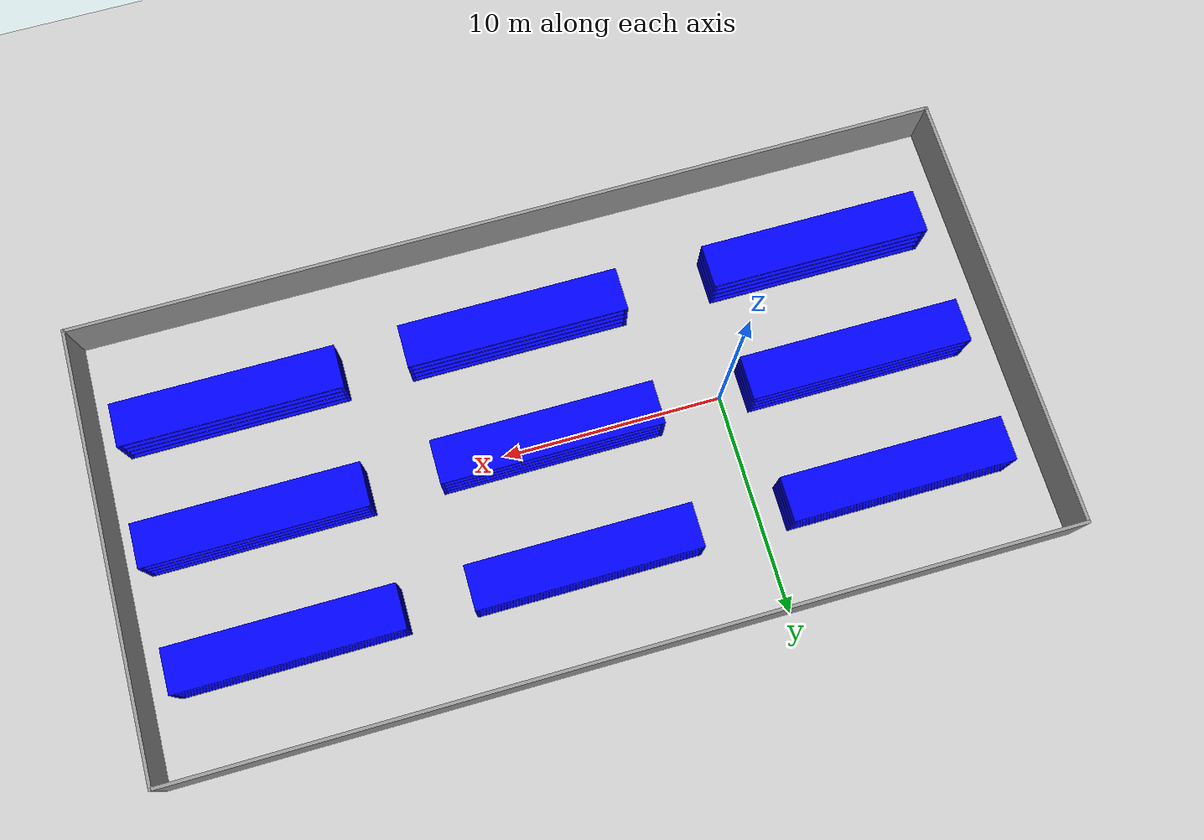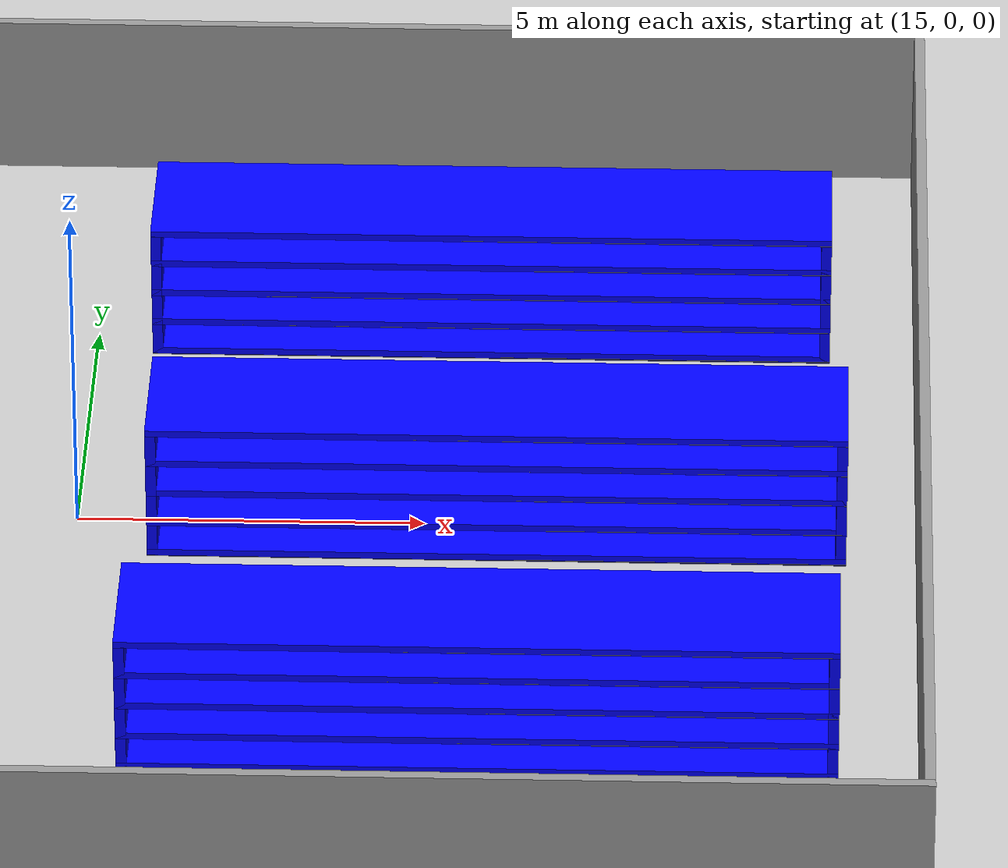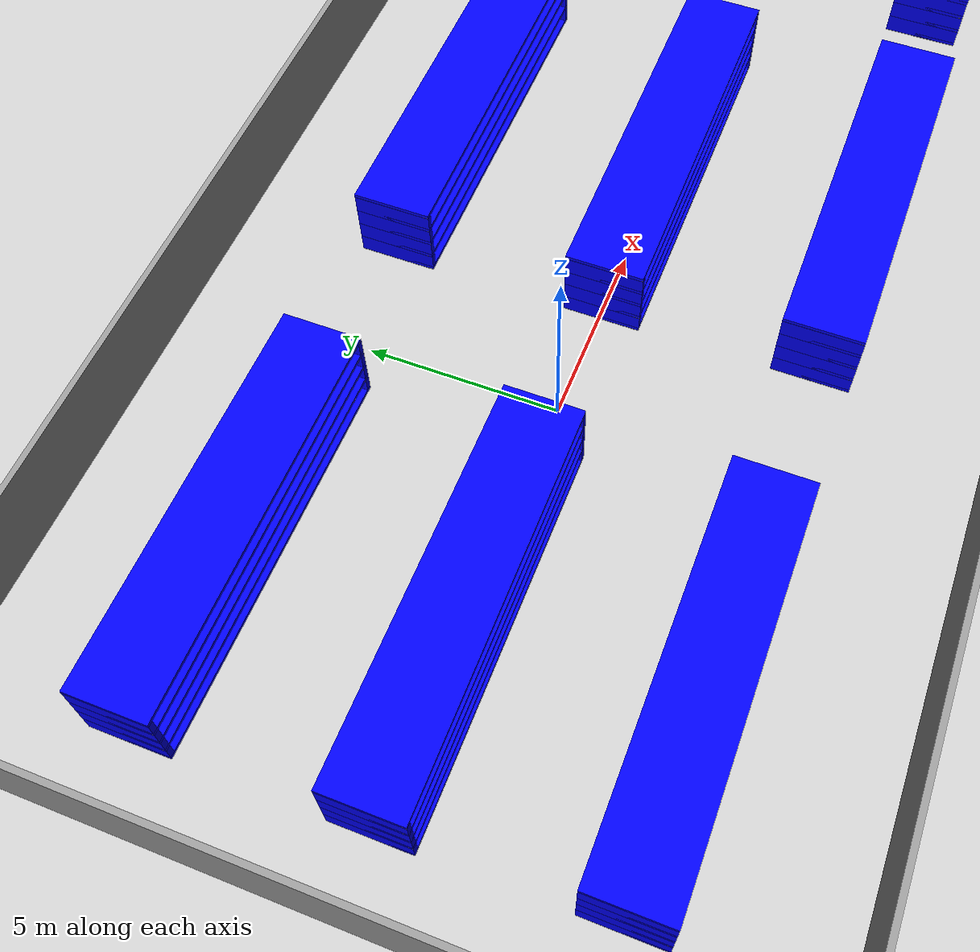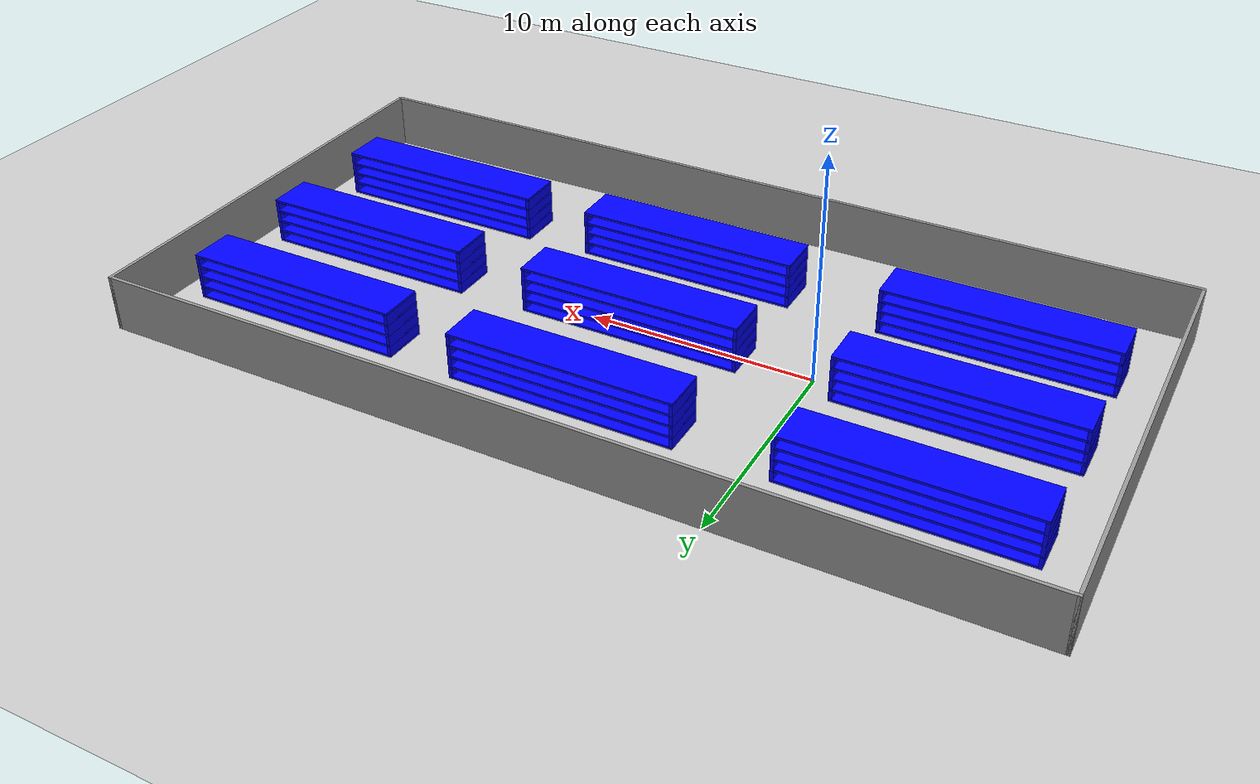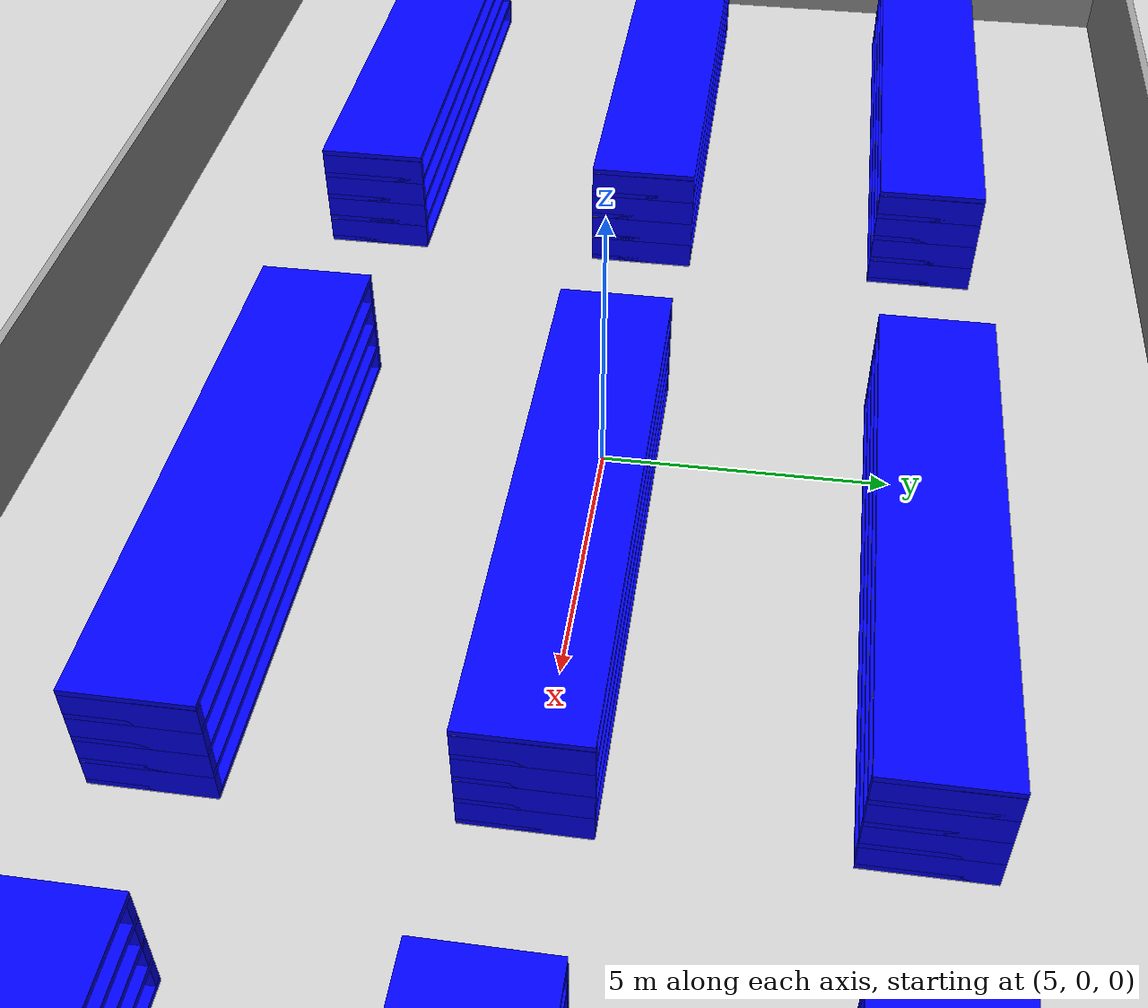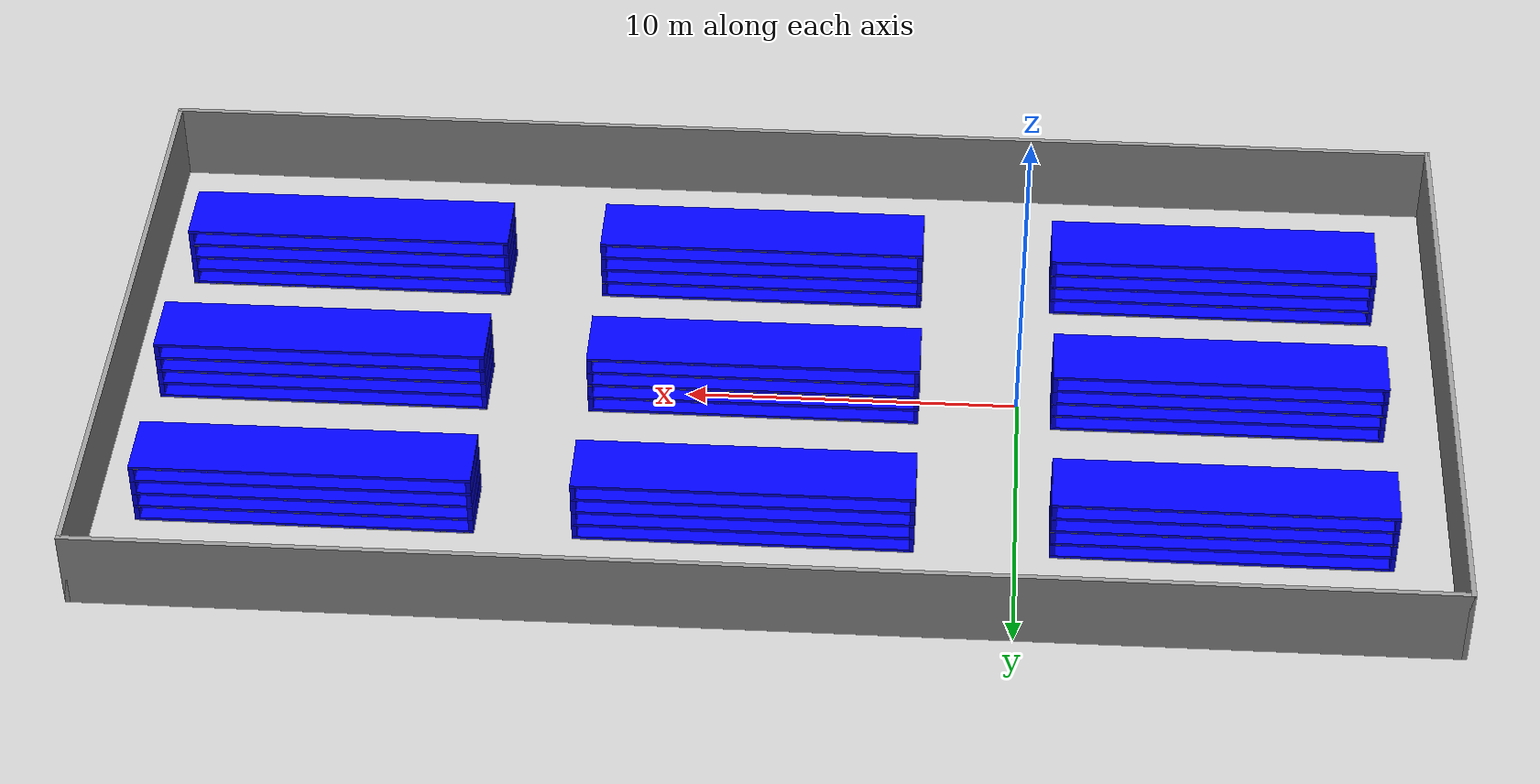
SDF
<sdf version="1.6">
 <world name="default">
  <light name="sun" type="directional">
   <pose>0 0 10 0 -0 0</pose>
   <diffuse>0.8 0.8 0.8 1</diffuse>
   <specular>0.1 0.1 0.1 1</specular>
   <attenuation>
    <range>1000</range>
    <constant>0.9</constant>
    <linear>0.01</linear>
    <quadratic>0.001</quadratic>
   </attenuation>
   <direction>-0.5 0.5 -1</direction>
  </light>
  <model name="ground_plane">
   <static>1</static>
   <link name="link">
    <collision name="collision">
     <geometry><plane><normal>0 0 1</normal><size>100 100</size></plane></geometry>
     <surface><friction><ode><mu>100</mu><mu2>50</mu2></ode></friction></surface>
    </collision>
    <visual name="visual">
     <cast_shadows>0</cast_shadows>
     <geometry><plane><normal>0 0 1</normal><size>100 100</size></plane></geometry>
     <material>
      <script><uri>file://media/materials/scripts/gazebo.material</uri><name>Gazebo/Grey</name></script>
     </material>
    </visual>
   </link>
  </model>
  <gravity>0 0 -9.8</gravity>
  <magnetic_field>6e-06 2.3e-05 -4.2e-05</magnetic_field>
  <atmosphere type="adiabatic"/>
  <physics name="default_physics" default="0" type="ode">
   <max_step_size>0.001</max_step_size>
   <real_time_factor>1</real_time_factor>
   <real_time_update_rate>1000</real_time_update_rate>
  </physics>
  <scene><ambient>0.4 0.4 0.4 1</ambient><background>0.7 0.7 0.7 1</background><shadows>1</shadows></scene>
  <spherical_coordinates>
   <surface_model>EARTH_WGS84</surface_model>
   <latitude_deg>0</latitude_deg>
   <longitude_deg>0</longitude_deg>
   <elevation>0</elevation>
   <heading_deg>0</heading_deg>
  </spherical_coordinates>
  <model name="empty_world">
   <pose>7.18379 -0.043522 0 0 -0 0</pose>
   <link name="Wall_0">
    <collision name="Wall_0_Collision">
     <geometry><box><size>40.04 0.15 2.5</size></box></geometry>
     <pose>0 0 1.25 0 -0 0</pose>
    </collision>
    <visual name="Wall_0_Visual">
     <pose>0 0 1.25 0 -0 0</pose>
     <geometry><box><size>40.04 0.15 2.5</size></box></geometry>
     <material>
      <script><uri>file://media/materials/scripts/gazebo.material</uri><name>Gazebo/Grey</name></script>
      <ambient>1 1 1 1</ambient>
     </material>
    </visual>
    <pose>0 -10 0 0 -0 0</pose>
   </link>
   <link name="Wall_13">
    <collision name="Wall_13_Collision">
     <geometry><box><size>20.15 0.15 2.5</size></box></geometry>
     <pose>0 0 1.25 0 -0 0</pose>
    </collision>
    <visual name="Wall_13_Visual">
     <pose>0 0 1.25 0 -0 0</pose>
     <geometry><box><size>20.15 0.15 2.5</size></box></geometry>
     <material>
      <script><uri>file://media/materials/scripts/gazebo.material</uri><name>Gazebo/Grey</name></script>
      <ambient>1 1 1 1</ambient>
     </material>
    </visual>
    <pose>19.945 0 0 0 -0 1.5708</pose>
   </link>
   <link name="Wall_2">
    <collision name="Wall_2_Collision">
     <geometry><box><size>20.15 0.15 2.5</size></box></geometry>
     <pose>0 0 1.25 0 -0 0</pose>
    </collision>
    <visual name="Wall_2_Visual">
     <pose>0 0 1.25 0 -0 0</pose>
     <geometry><box><size>20.15 0.15 2.5</size></box></geometry>
     <material>
      <script><uri>file://media/materials/scripts/gazebo.material</uri><name>Gazebo/Grey</name></script>
      <ambient>1 1 1 1</ambient>
     </material>
    </visual>
    <pose>-19.945 0 0 0 0 -1.5708</pose>
   </link>
   <link name="Wall_4">
    <collision name="Wall_4_Collision">
     <geometry><box><size>40.0405 0.15 2.5</size></box></geometry>
     <pose>0 0 1.25 0 -0 0</pose>
    </collision>
    <visual name="Wall_4_Visual">
     <pose>0 0 1.25 0 -0 0</pose>
     <geometry><box><size>40.0405 0.15 2.5</size></box></geometry>
     <material>
      <script><uri>file://media/materials/scripts/gazebo.material</uri><name>Gazebo/Grey</name></script>
      <ambient>1 1 1 1</ambient>
     </material>
    </visual>
    <pose>0 10 0 0 -0 0</pose>
   </link>
   <static>1</static>
  </model>
  <model name="blue_shelf">
   <pose>-6.00982 -0.023754 0 0 -0 0</pose>
   <link name="Floor_18">
    <collision name="Floor_18_Collision">
     <geometry><box><size>10 2 0.1</size></box></geometry>
     <pose>0 0 0.05 0 -0 0</pose>
    </collision>
    <visual name="Floor_18_Visual">
     <pose>0 0 0.05 0 -0 0</pose>
     <geometry><box><size>10 2 0.1</size></box></geometry>
     <material>
      <script><uri>file://media/materials/scripts/gazebo.material</uri><name>Gazebo/Grey</name></script>
      <ambient>0 0 1 1</ambient>
     </material>
    </visual>
    <pose>0 0 0.01 0 -0 0</pose>
   </link>
   <link name="Floor_23">
    <collision name="Floor_23_Collision">
     <geometry><box><size>10 2 0.1</size></box></geometry>
     <pose>0 0 0.05 0 -0 0</pose>
    </collision>
    <visual name="Floor_23_Visual">
     <pose>0 0 0.05 0 -0 0</pose>
     <geometry><box><size>10 2 0.1</size></box></geometry>
     <material>
      <script><uri>file://media/materials/scripts/gazebo.material</uri><name>Gazebo/Grey</name></script>
      <ambient>0 0 1 1</ambient>
     </material>
    </visual>
    <pose>0 0 0.51 0 -0 0</pose>
   </link>
   <link name="Floor_24">
    <collision name="Floor_24_Collision">
     <geometry><box><size>10 2 0.1</size></box></geometry>
     <pose>0 0 0.05 0 -0 0</pose>
    </collision>
    <visual name="Floor_24_Visual">
     <pose>0 0 0.05 0 -0 0</pose>
     <geometry><box><size>10 2 0.1</size></box></geometry>
     <material>
      <script><uri>file://media/materials/scripts/gazebo.material</uri><name>Gazebo/Grey</name></script>
      <ambient>0 0 1 1</ambient>
     </material>
    </visual>
    <pose>0 0 1.01 0 -0 0</pose>
   </link>
   <link name="Floor_25">
    <collision name="Floor_25_Collision">
     <geometry><box><size>10 2 0.1</size></box></geometry>
     <pose>0 0 0.05 0 -0 0</pose>
    </collision>
    <visual name="Floor_25_Visual">
     <pose>0 0 0.05 0 -0 0</pose>
     <geometry><box><size>10 2 0.1</size></box></geometry>
     <material>
      <script><uri>file://media/materials/scripts/gazebo.material</uri><name>Gazebo/Grey</name></script>
      <ambient>0 0 1 1</ambient>
     </material>
    </visual>
    <pose>0 0 1.51 0 -0 0</pose>
   </link>
   <link name="Floor_26">
    <collision name="Floor_26_Collision">
     <geometry><box><size>10 2 0.1</size></box></geometry>
     <pose>0 0 0.05 0 -0 0</pose>
    </collision>
    <visual name="Floor_26_Visual">
     <pose>0 0 0.05 0 -0 0</pose>
     <geometry><box><size>10 2 0.1</size></box></geometry>
     <material>
      <script><uri>file://media/materials/scripts/gazebo.material</uri><name>Gazebo/Grey</name></script>
      <ambient>0 0 1 1</ambient>
     </material>
    </visual>
    <pose>0 0 2.01 0 -0 0</pose>
   </link>
   <link name="Wall_111">
    <collision name="Wall_111_Collision">
     <geometry><box><size>10 0.15 0.01</size></box></geometry>
     <pose>0 0 0.005 0 -0 0</pose>
    </collision>
    <visual name="Wall_111_Visual">
     <pose>0 0 0.005 0 -0 0</pose>
     <geometry><box><size>10 0.15 0.01</size></box></geometry>
     <material>
      <script><uri>file://media/materials/scripts/gazebo.material</uri><name>Gazebo/Grey</name></script>
      <ambient>1 1 1 1</ambient>
     </material>
    </visual>
    <pose>0 0.925 0.51 0 -0 0</pose>
   </link>
   <link name="Wall_112">
    <collision name="Wall_112_Collision">
     <geometry><box><size>2 0.15 0.5</size></box></geometry>
     <pose>0 0 0.25 0 -0 0</pose>
    </collision>
    <visual name="Wall_112_Visual">
     <pose>0 0 0.25 0 -0 0</pose>
     <geometry><box><size>2 0.15 0.5</size></box></geometry>
     <material>
      <script><uri>file://media/materials/scripts/gazebo.material</uri><name>Gazebo/Grey</name></script>
      <ambient>0 0 1 1</ambient>
     </material>
    </visual>
    <pose>4.925 0 0.51 0 0 -1.5708</pose>
   </link>
   <link name="Wall_113">
    <collision name="Wall_113_Collision">
     <geometry><box><size>10 0.15 0.01</size></box></geometry>
     <pose>0 0 0.005 0 -0 0</pose>
    </collision>
    <visual name="Wall_113_Visual">
     <pose>0 0 0.005 0 -0 0</pose>
     <geometry><box><size>10 0.15 0.01</size></box></geometry>
     <material>
      <script><uri>file://media/materials/scripts/gazebo.material</uri><name>Gazebo/Grey</name></script>
      <ambient>1 1 1 1</ambient>
     </material>
    </visual>
    <pose>0 -0.925 0.51 0 -0 3.14159</pose>
   </link>
   <link name="Wall_114">
    <collision name="Wall_114_Collision">
     <geometry><box><size>2 0.15 0.5</size></box></geometry>
     <pose>0 0 0.25 0 -0 0</pose>
    </collision>
    <visual name="Wall_114_Visual">
     <pose>0 0 0.25 0 -0 0</pose>
     <geometry><box><size>2 0.15 0.5</size></box></geometry>
     <material>
      <script><uri>file://media/materials/scripts/gazebo.material</uri><name>Gazebo/Grey</name></script>
      <ambient>0 0 1 1</ambient>
     </material>
    </visual>
    <pose>-4.925 0 0.51 0 -0 1.5708</pose>
   </link>
   <link name="Wall_115">
    <collision name="Wall_115_Collision">
     <geometry><box><size>10 0.15 0.01</size></box></geometry>
     <pose>0 0 0.005 0 -0 0</pose>
    </collision>
    <visual name="Wall_115_Visual">
     <pose>0 0 0.005 0 -0 0</pose>
     <geometry><box><size>10 0.15 0.01</size></box></geometry>
     <material>
      <script><uri>file://media/materials/scripts/gazebo.material</uri><name>Gazebo/Grey</name></script>
      <ambient>1 1 1 1</ambient>
     </material>
    </visual>
    <pose>0 0.925 1.01 0 -0 0</pose>
   </link>
   <link name="Wall_116">
    <collision name="Wall_116_Collision">
     <geometry><box><size>2 0.15 0.5</size></box></geometry>
     <pose>0 0 0.25 0 -0 0</pose>
    </collision>
    <visual name="Wall_116_Visual">
     <pose>0 0 0.25 0 -0 0</pose>
     <geometry><box><size>2 0.15 0.5</size></box></geometry>
     <material>
      <script><uri>file://media/materials/scripts/gazebo.material</uri><name>Gazebo/Grey</name></script>
      <ambient>0 0 1 1</ambient>
     </material>
    </visual>
    <pose>4.925 0 1.01 0 0 -1.5708</pose>
   </link>
   <link name="Wall_117">
    <collision name="Wall_117_Collision">
     <geometry><box><size>10 0.15 0.01</size></box></geometry>
     <pose>0 0 0.005 0 -0 0</pose>
    </collision>
    <visual name="Wall_117_Visual">
     <pose>0 0 0.005 0 -0 0</pose>
     <geometry><box><size>10 0.15 0.01</size></box></geometry>
     <material>
      <script><uri>file://media/materials/scripts/gazebo.material</uri><name>Gazebo/Grey</name></script>
      <ambient>1 1 1 1</ambient>
     </material>
    </visual>
    <pose>0 -0.925 1.01 0 -0 3.14159</pose>
   </link>
   <link name="Wall_118">
    <collision name="Wall_118_Collision">
     <geometry><box><size>2 0.15 0.5</size></box></geometry>
     <pose>0 0 0.25 0 -0 0</pose>
    </collision>
    <visual name="Wall_118_Visual">
     <pose>0 0 0.25 0 -0 0</pose>
     <geometry><box><size>2 0.15 0.5</size></box></geometry>
     <material>
      <script><uri>file://media/materials/scripts/gazebo.material</uri><name>Gazebo/Grey</name></script>
      <ambient>0 0 1 1</ambient>
     </material>
    </visual>
    <pose>-4.925 0 1.01 0 -0 1.5708</pose>
   </link>
   <link name="Wall_119">
    <collision name="Wall_119_Collision">
     <geometry><box><size>10 0.15 0.01</size></box></geometry>
     <pose>0 0 0.005 0 -0 0</pose>
    </collision>
    <visual name="Wall_119_Visual">
     <pose>0 0 0.005 0 -0 0</pose>
     <geometry><box><size>10 0.15 0.01</size></box></geometry>
     <material>
      <script><uri>file://media/materials/scripts/gazebo.material</uri><name>Gazebo/Grey</name></script>
      <ambient>1 1 1 1</ambient>
     </material>
    </visual>
    <pose>0 0.925 1.51 0 -0 0</pose>
   </link>
   <link name="Wall_120">
    <collision name="Wall_120_Collision">
     <geometry><box><size>2 0.15 0.5</size></box></geometry>
     <pose>0 0 0.25 0 -0 0</pose>
    </collision>
    <visual name="Wall_120_Visual">
     <pose>0 0 0.25 0 -0 0</pose>
     <geometry><box><size>2 0.15 0.5</size></box></geometry>
     <material>
      <script><uri>file://media/materials/scripts/gazebo.material</uri><name>Gazebo/Grey</name></script>
      <ambient>0 0 1 1</ambient>
     </material>
    </visual>
    <pose>4.925 0 1.51 0 0 -1.5708</pose>
   </link>
   <link name="Wall_121">
    <collision name="Wall_121_Collision">
     <geometry><box><size>10 0.15 0.01</size></box></geometry>
     <pose>0 0 0.005 0 -0 0</pose>
    </collision>
    <visual name="Wall_121_Visual">
     <pose>0 0 0.005 0 -0 0</pose>
     <geometry><box><size>10 0.15 0.01</size></box></geometry>
     <material>
      <script><uri>file://media/materials/scripts/gazebo.material</uri><name>Gazebo/Grey</name></script>
      <ambient>1 1 1 1</ambient>
     </material>
    </visual>
    <pose>0 -0.925 1.51 0 -0 3.14159</pose>
   </link>
   <link name="Wall_122">
    <collision name="Wall_122_Collision">
     <geometry><box><size>2 0.15 0.5</size></box></geometry>
     <pose>0 0 0.25 0 -0 0</pose>
    </collision>
    <visual name="Wall_122_Visual">
     <pose>0 0 0.25 0 -0 0</pose>
     <geometry><box><size>2 0.15 0.5</size></box></geometry>
     <material>
      <script><uri>file://media/materials/scripts/gazebo.material</uri><name>Gazebo/Grey</name></script>
      <ambient>0 0 1 1</ambient>
     </material>
    </visual>
    <pose>-4.925 0 1.51 0 -0 1.5708</pose>
   </link>
   <link name="Wall_123">
    <collision name="Wall_123_Collision">
     <geometry><box><size>10 0.15 0.01</size></box></geometry>
     <pose>0 0 0.005 0 -0 0</pose>
    </collision>
    <visual name="Wall_123_Visual">
     <pose>0 0 0.005 0 -0 0</pose>
     <geometry><box><size>10 0.15 0.01</size></box></geometry>
     <material>
      <script><uri>file://media/materials/scripts/gazebo.material</uri><name>Gazebo/Grey</name></script>
      <ambient>1 1 1 1</ambient>
     </material>
    </visual>
    <pose>0 0.925 2.01 0 -0 0</pose>
   </link>
   <link name="Wall_124">
    <collision name="Wall_124_Collision">
     <geometry><box><size>2 0.15 0.01</size></box></geometry>
     <pose>0 0 0.005 0 -0 0</pose>
    </collision>
    <visual name="Wall_124_Visual">
     <pose>0 0 0.005 0 -0 0</pose>
     <geometry><box><size>2 0.15 0.01</size></box></geometry>
     <material>
      <script><uri>file://media/materials/scripts/gazebo.material</uri><name>Gazebo/Grey</name></script>
      <ambient>0 0 1 1</ambient>
     </material>
    </visual>
    <pose>4.925 0 2.01 0 0 -1.5708</pose>
   </link>
   <link name="Wall_125">
    <collision name="Wall_125_Collision">
     <geometry><box><size>10 0.15 0.01</size></box></geometry>
     <pose>0 0 0.005 0 -0 0</pose>
    </collision>
    <visual name="Wall_125_Visual">
     <pose>0 0 0.005 0 -0 0</pose>
     <geometry><box><size>10 0.15 0.01</size></box></geometry>
     <material>
      <script><uri>file://media/materials/scripts/gazebo.material</uri><name>Gazebo/Grey</name></script>
      <ambient>1 1 1 1</ambient>
     </material>
    </visual>
    <pose>0 -0.925 2.01 0 -0 3.14159</pose>
   </link>
   <link name="Wall_126">
    <collision name="Wall_126_Collision">
     <geometry><box><size>2 0.15 0.01</size></box></geometry>
     <pose>0 0 0.005 0 -0 0</pose>
    </collision>
    <visual name="Wall_126_Visual">
     <pose>0 0 0.005 0 -0 0</pose>
     <geometry><box><size>2 0.15 0.01</size></box></geometry>
     <material>
      <script><uri>file://media/materials/scripts/gazebo.material</uri><name>Gazebo/Grey</name></script>
      <ambient>0 0 1 1</ambient>
     </material>
    </visual>
    <pose>-4.925 0 2.01 0 -0 1.5708</pose>
   </link>
   <link name="Wall_60">
    <collision name="Wall_60_Collision">
     <geometry><box><size>10 0.15 0.01</size></box></geometry>
     <pose>0 0 0.005 0 -0 0</pose>
    </collision>
    <visual name="Wall_60_Visual">
     <pose>0 0 0.005 0 -0 0</pose>
     <geometry><box><size>10 0.15 0.01</size></box></geometry>
     <material>
      <script><uri>file://media/materials/scripts/gazebo.material</uri><name>Gazebo/Grey</name></script>
      <ambient>0 0 0.498039 1</ambient>
     </material>
    </visual>
    <pose>0 0.925 0 0 -0 0</pose>
   </link>
   <link name="Wall_61">
    <collision name="Wall_61_Collision">
     <geometry><box><size>2 0.15 0.01</size></box></geometry>
     <pose>0 0 0.005 0 -0 0</pose>
    </collision>
    <visual name="Wall_61_Visual">
     <pose>0 0 0.005 0 -0 0</pose>
     <geometry><box><size>2 0.15 0.01</size></box></geometry>
     <material>
      <script><uri>file://media/materials/scripts/gazebo.material</uri><name>Gazebo/Grey</name></script>
      <ambient>0 0 0.498039 1</ambient>
     </material>
    </visual>
    <pose>4.925 0 0 0 0 -1.5708</pose>
   </link>
   <link name="Wall_62">
    <collision name="Wall_62_Collision">
     <geometry><box><size>10 0.15 0.01</size></box></geometry>
     <pose>0 0 0.005 0 -0 0</pose>
    </collision>
    <visual name="Wall_62_Visual">
     <pose>0 0 0.005 0 -0 0</pose>
     <geometry><box><size>10 0.15 0.01</size></box></geometry>
     <material>
      <script><uri>file://media/materials/scripts/gazebo.material</uri><name>Gazebo/Grey</name></script>
      <ambient>0 0 0.498039 1</ambient>
     </material>
    </visual>
    <pose>0 -0.925 0 0 -0 3.14159</pose>
   </link>
   <link name="Wall_63">
    <collision name="Wall_63_Collision">
     <geometry><box><size>2 0.15 0.01</size></box></geometry>
     <pose>0 0 0.005 0 -0 0</pose>
    </collision>
    <visual name="Wall_63_Visual">
     <pose>0 0 0.005 0 -0 0</pose>
     <geometry><box><size>2 0.15 0.01</size></box></geometry>
     <material>
      <script><uri>file://media/materials/scripts/gazebo.material</uri><name>Gazebo/Grey</name></script>
      <ambient>0 0 0.498039 1</ambient>
     </material>
    </visual>
    <pose>-4.925 0 0 0 -0 1.5708</pose>
   </link>
   <link name="Wall_91">
    <collision name="Wall_91_Collision">
     <geometry><box><size>10 0.15 0.01</size></box></geometry>
     <pose>0 0 0.005 0 -0 0</pose>
    </collision>
    <visual name="Wall_91_Visual">
     <pose>0 0 0.005 0 -0 0</pose>
     <geometry><box><size>10 0.15 0.01</size></box></geometry>
     <material>
      <script><uri>file://media/materials/scripts/gazebo.material</uri><name>Gazebo/Grey</name></script>
      <ambient>1 1 1 1</ambient>
     </material>
    </visual>
    <pose>0 0.925 0.01 0 -0 0</pose>
   </link>
   <link name="Wall_92">
    <collision name="Wall_92_Collision">
     <geometry><box><size>2 0.15 0.5</size></box></geometry>
     <pose>0 0 0.25 0 -0 0</pose>
    </collision>
    <visual name="Wall_92_Visual">
     <pose>0 0 0.25 0 -0 0</pose>
     <geometry><box><size>2 0.15 0.5</size></box></geometry>
     <material>
      <script><uri>file://media/materials/scripts/gazebo.material</uri><name>Gazebo/Grey</name></script>
      <ambient>0 0 1 1</ambient>
     </material>
    </visual>
    <pose>4.925 0 0.01 0 0 -1.5708</pose>
   </link>
   <link name="Wall_93">
    <collision name="Wall_93_Collision">
     <geometry><box><size>10 0.15 0.01</size></box></geometry>
     <pose>0 0 0.005 0 -0 0</pose>
    </collision>
    <visual name="Wall_93_Visual">
     <pose>0 0 0.005 0 -0 0</pose>
     <geometry><box><size>10 0.15 0.01</size></box></geometry>
     <material>
      <script><uri>file://media/materials/scripts/gazebo.material</uri><name>Gazebo/Grey</name></script>
      <ambient>1 1 1 1</ambient>
     </material>
    </visual>
    <pose>0 -0.925 0.01 0 -0 3.14159</pose>
   </link>
   <link name="Wall_94">
    <collision name="Wall_94_Collision">
     <geometry><box><size>2 0.15 0.5</size></box></geometry>
     <pose>0 0 0.25 0 -0 0</pose>
    </collision>
    <visual name="Wall_94_Visual">
     <pose>0 0 0.25 0 -0 0</pose>
     <geometry><box><size>2 0.15 0.5</size></box></geometry>
     <material>
      <script><uri>file://media/materials/scripts/gazebo.material</uri><name>Gazebo/Grey</name></script>
      <ambient>0 0 1 1</ambient>
     </material>
    </visual>
    <pose>-4.925 0 0.01 0 -0 1.5708</pose>
   </link>
   <static>1</static>
  </model>
  <model name="blue_shelf_0">
   <pose>-6.00751 5.56807 0 0 -0 0</pose>
   <link name="Floor_18">
    <collision name="Floor_18_Collision">
     <geometry><box><size>10 2 0.1</size></box></geometry>
     <pose>0 0 0.05 0 -0 0</pose>
    </collision>
    <visual name="Floor_18_Visual">
     <pose>0 0 0.05 0 -0 0</pose>
     <geometry><box><size>10 2 0.1</size></box></geometry>
     <material>
      <script><uri>file://media/materials/scripts/gazebo.material</uri><name>Gazebo/Grey</name></script>
      <ambient>0 0 1 1</ambient>
     </material>
    </visual>
    <pose>0 0 0.01 0 -0 0</pose>
   </link>
   <link name="Floor_23">
    <collision name="Floor_23_Collision">
     <geometry><box><size>10 2 0.1</size></box></geometry>
     <pose>0 0 0.05 0 -0 0</pose>
    </collision>
    <visual name="Floor_23_Visual">
     <pose>0 0 0.05 0 -0 0</pose>
     <geometry><box><size>10 2 0.1</size></box></geometry>
     <material>
      <script><uri>file://media/materials/scripts/gazebo.material</uri><name>Gazebo/Grey</name></script>
      <ambient>0 0 1 1</ambient>
     </material>
    </visual>
    <pose>0 0 0.51 0 -0 0</pose>
   </link>
   <link name="Floor_24">
    <collision name="Floor_24_Collision">
     <geometry><box><size>10 2 0.1</size></box></geometry>
     <pose>0 0 0.05 0 -0 0</pose>
    </collision>
    <visual name="Floor_24_Visual">
     <pose>0 0 0.05 0 -0 0</pose>
     <geometry><box><size>10 2 0.1</size></box></geometry>
     <material>
      <script><uri>file://media/materials/scripts/gazebo.material</uri><name>Gazebo/Grey</name></script>
      <ambient>0 0 1 1</ambient>
     </material>
    </visual>
    <pose>0 0 1.01 0 -0 0</pose>
   </link>
   <link name="Floor_25">
    <collision name="Floor_25_Collision">
     <geometry><box><size>10 2 0.1</size></box></geometry>
     <pose>0 0 0.05 0 -0 0</pose>
    </collision>
    <visual name="Floor_25_Visual">
     <pose>0 0 0.05 0 -0 0</pose>
     <geometry><box><size>10 2 0.1</size></box></geometry>
     <material>
      <script><uri>file://media/materials/scripts/gazebo.material</uri><name>Gazebo/Grey</name></script>
      <ambient>0 0 1 1</ambient>
     </material>
    </visual>
    <pose>0 0 1.51 0 -0 0</pose>
   </link>
   <link name="Floor_26">
    <collision name="Floor_26_Collision">
     <geometry><box><size>10 2 0.1</size></box></geometry>
     <pose>0 0 0.05 0 -0 0</pose>
    </collision>
    <visual name="Floor_26_Visual">
     <pose>0 0 0.05 0 -0 0</pose>
     <geometry><box><size>10 2 0.1</size></box></geometry>
     <material>
      <script><uri>file://media/materials/scripts/gazebo.material</uri><name>Gazebo/Grey</name></script>
      <ambient>0 0 1 1</ambient>
     </material>
    </visual>
    <pose>0 0 2.01 0 -0 0</pose>
   </link>
   <link name="Wall_111">
    <collision name="Wall_111_Collision">
     <geometry><box><size>10 0.15 0.01</size></box></geometry>
     <pose>0 0 0.005 0 -0 0</pose>
    </collision>
    <visual name="Wall_111_Visual">
     <pose>0 0 0.005 0 -0 0</pose>
     <geometry><box><size>10 0.15 0.01</size></box></geometry>
     <material>
      <script><uri>file://media/materials/scripts/gazebo.material</uri><name>Gazebo/Grey</name></script>
      <ambient>1 1 1 1</ambient>
     </material>
    </visual>
    <pose>0 0.925 0.51 0 -0 0</pose>
   </link>
   <link name="Wall_112">
    <collision name="Wall_112_Collision">
     <geometry><box><size>2 0.15 0.5</size></box></geometry>
     <pose>0 0 0.25 0 -0 0</pose>
    </collision>
    <visual name="Wall_112_Visual">
     <pose>0 0 0.25 0 -0 0</pose>
     <geometry><box><size>2 0.15 0.5</size></box></geometry>
     <material>
      <script><uri>file://media/materials/scripts/gazebo.material</uri><name>Gazebo/Grey</name></script>
      <ambient>0 0 1 1</ambient>
     </material>
    </visual>
    <pose>4.925 0 0.51 0 0 -1.5708</pose>
   </link>
   <link name="Wall_113">
    <collision name="Wall_113_Collision">
     <geometry><box><size>10 0.15 0.01</size></box></geometry>
     <pose>0 0 0.005 0 -0 0</pose>
    </collision>
    <visual name="Wall_113_Visual">
     <pose>0 0 0.005 0 -0 0</pose>
     <geometry><box><size>10 0.15 0.01</size></box></geometry>
     <material>
      <script><uri>file://media/materials/scripts/gazebo.material</uri><name>Gazebo/Grey</name></script>
      <ambient>1 1 1 1</ambient>
     </material>
    </visual>
    <pose>0 -0.925 0.51 0 -0 3.14159</pose>
   </link>
   <link name="Wall_114">
    <collision name="Wall_114_Collision">
     <geometry><box><size>2 0.15 0.5</size></box></geometry>
     <pose>0 0 0.25 0 -0 0</pose>
    </collision>
    <visual name="Wall_114_Visual">
     <pose>0 0 0.25 0 -0 0</pose>
     <geometry><box><size>2 0.15 0.5</size></box></geometry>
     <material>
      <script><uri>file://media/materials/scripts/gazebo.material</uri><name>Gazebo/Grey</name></script>
      <ambient>0 0 1 1</ambient>
     </material>
    </visual>
    <pose>-4.925 0 0.51 0 -0 1.5708</pose>
   </link>
   <link name="Wall_115">
    <collision name="Wall_115_Collision">
     <geometry><box><size>10 0.15 0.01</size></box></geometry>
     <pose>0 0 0.005 0 -0 0</pose>
    </collision>
    <visual name="Wall_115_Visual">
     <pose>0 0 0.005 0 -0 0</pose>
     <geometry><box><size>10 0.15 0.01</size></box></geometry>
     <material>
      <script><uri>file://media/materials/scripts/gazebo.material</uri><name>Gazebo/Grey</name></script>
      <ambient>1 1 1 1</ambient>
     </material>
    </visual>
    <pose>0 0.925 1.01 0 -0 0</pose>
   </link>
   <link name="Wall_116">
    <collision name="Wall_116_Collision">
     <geometry><box><size>2 0.15 0.5</size></box></geometry>
     <pose>0 0 0.25 0 -0 0</pose>
    </collision>
    <visual name="Wall_116_Visual">
     <pose>0 0 0.25 0 -0 0</pose>
     <geometry><box><size>2 0.15 0.5</size></box></geometry>
     <material>
      <script><uri>file://media/materials/scripts/gazebo.material</uri><name>Gazebo/Grey</name></script>
      <ambient>0 0 1 1</ambient>
     </material>
    </visual>
    <pose>4.925 0 1.01 0 0 -1.5708</pose>
   </link>
   <link name="Wall_117">
    <collision name="Wall_117_Collision">
     <geometry><box><size>10 0.15 0.01</size></box></geometry>
     <pose>0 0 0.005 0 -0 0</pose>
    </collision>
    <visual name="Wall_117_Visual">
     <pose>0 0 0.005 0 -0 0</pose>
     <geometry><box><size>10 0.15 0.01</size></box></geometry>
     <material>
      <script><uri>file://media/materials/scripts/gazebo.material</uri><name>Gazebo/Grey</name></script>
      <ambient>1 1 1 1</ambient>
     </material>
    </visual>
    <pose>0 -0.925 1.01 0 -0 3.14159</pose>
   </link>
   <link name="Wall_118">
    <collision name="Wall_118_Collision">
     <geometry><box><size>2 0.15 0.5</size></box></geometry>
     <pose>0 0 0.25 0 -0 0</pose>
    </collision>
    <visual name="Wall_118_Visual">
     <pose>0 0 0.25 0 -0 0</pose>
     <geometry><box><size>2 0.15 0.5</size></box></geometry>
     <material>
      <script><uri>file://media/materials/scripts/gazebo.material</uri><name>Gazebo/Grey</name></script>
      <ambient>0 0 1 1</ambient>
     </material>
    </visual>
    <pose>-4.925 0 1.01 0 -0 1.5708</pose>
   </link>
   <link name="Wall_119">
    <collision name="Wall_119_Collision">
     <geometry><box><size>10 0.15 0.01</size></box></geometry>
     <pose>0 0 0.005 0 -0 0</pose>
    </collision>
    <visual name="Wall_119_Visual">
     <pose>0 0 0.005 0 -0 0</pose>
     <geometry><box><size>10 0.15 0.01</size></box></geometry>
     <material>
      <script><uri>file://media/materials/scripts/gazebo.material</uri><name>Gazebo/Grey</name></script>
      <ambient>1 1 1 1</ambient>
     </material>
    </visual>
    <pose>0 0.925 1.51 0 -0 0</pose>
   </link>
   <link name="Wall_120">
    <collision name="Wall_120_Collision">
     <geometry><box><size>2 0.15 0.5</size></box></geometry>
     <pose>0 0 0.25 0 -0 0</pose>
    </collision>
    <visual name="Wall_120_Visual">
     <pose>0 0 0.25 0 -0 0</pose>
     <geometry><box><size>2 0.15 0.5</size></box></geometry>
     <material>
      <script><uri>file://media/materials/scripts/gazebo.material</uri><name>Gazebo/Grey</name></script>
      <ambient>0 0 1 1</ambient>
     </material>
    </visual>
    <pose>4.925 0 1.51 0 0 -1.5708</pose>
   </link>
   <link name="Wall_121">
    <collision name="Wall_121_Collision">
     <geometry><box><size>10 0.15 0.01</size></box></geometry>
     <pose>0 0 0.005 0 -0 0</pose>
    </collision>
    <visual name="Wall_121_Visual">
     <pose>0 0 0.005 0 -0 0</pose>
     <geometry><box><size>10 0.15 0.01</size></box></geometry>
     <material>
      <script><uri>file://media/materials/scripts/gazebo.material</uri><name>Gazebo/Grey</name></script>
      <ambient>1 1 1 1</ambient>
     </material>
    </visual>
    <pose>0 -0.925 1.51 0 -0 3.14159</pose>
   </link>
   <link name="Wall_122">
    <collision name="Wall_122_Collision">
     <geometry><box><size>2 0.15 0.5</size></box></geometry>
     <pose>0 0 0.25 0 -0 0</pose>
    </collision>
    <visual name="Wall_122_Visual">
     <pose>0 0 0.25 0 -0 0</pose>
     <geometry><box><size>2 0.15 0.5</size></box></geometry>
     <material>
      <script><uri>file://media/materials/scripts/gazebo.material</uri><name>Gazebo/Grey</name></script>
      <ambient>0 0 1 1</ambient>
     </material>
    </visual>
    <pose>-4.925 0 1.51 0 -0 1.5708</pose>
   </link>
   <link name="Wall_123">
    <collision name="Wall_123_Collision">
     <geometry><box><size>10 0.15 0.01</size></box></geometry>
     <pose>0 0 0.005 0 -0 0</pose>
    </collision>
    <visual name="Wall_123_Visual">
     <pose>0 0 0.005 0 -0 0</pose>
     <geometry><box><size>10 0.15 0.01</size></box></geometry>
     <material>
      <script><uri>file://media/materials/scripts/gazebo.material</uri><name>Gazebo/Grey</name></script>
      <ambient>1 1 1 1</ambient>
     </material>
    </visual>
    <pose>0 0.925 2.01 0 -0 0</pose>
   </link>
   <link name="Wall_124">
    <collision name="Wall_124_Collision">
     <geometry><box><size>2 0.15 0.01</size></box></geometry>
     <pose>0 0 0.005 0 -0 0</pose>
    </collision>
    <visual name="Wall_124_Visual">
     <pose>0 0 0.005 0 -0 0</pose>
     <geometry><box><size>2 0.15 0.01</size></box></geometry>
     <material>
      <script><uri>file://media/materials/scripts/gazebo.material</uri><name>Gazebo/Grey</name></script>
      <ambient>0 0 1 1</ambient>
     </material>
    </visual>
    <pose>4.925 0 2.01 0 0 -1.5708</pose>
   </link>
   <link name="Wall_125">
    <collision name="Wall_125_Collision">
     <geometry><box><size>10 0.15 0.01</size></box></geometry>
     <pose>0 0 0.005 0 -0 0</pose>
    </collision>
    <visual name="Wall_125_Visual">
     <pose>0 0 0.005 0 -0 0</pose>
     <geometry><box><size>10 0.15 0.01</size></box></geometry>
     <material>
      <script><uri>file://media/materials/scripts/gazebo.material</uri><name>Gazebo/Grey</name></script>
      <ambient>1 1 1 1</ambient>
     </material>
    </visual>
    <pose>0 -0.925 2.01 0 -0 3.14159</pose>
   </link>
   <link name="Wall_126">
    <collision name="Wall_126_Collision">
     <geometry><box><size>2 0.15 0.01</size></box></geometry>
     <pose>0 0 0.005 0 -0 0</pose>
    </collision>
    <visual name="Wall_126_Visual">
     <pose>0 0 0.005 0 -0 0</pose>
     <geometry><box><size>2 0.15 0.01</size></box></geometry>
     <material>
      <script><uri>file://media/materials/scripts/gazebo.material</uri><name>Gazebo/Grey</name></script>
      <ambient>0 0 1 1</ambient>
     </material>
    </visual>
    <pose>-4.925 0 2.01 0 -0 1.5708</pose>
   </link>
   <link name="Wall_60">
    <collision name="Wall_60_Collision">
     <geometry><box><size>10 0.15 0.01</size></box></geometry>
     <pose>0 0 0.005 0 -0 0</pose>
    </collision>
    <visual name="Wall_60_Visual">
     <pose>0 0 0.005 0 -0 0</pose>
     <geometry><box><size>10 0.15 0.01</size></box></geometry>
     <material>
      <script><uri>file://media/materials/scripts/gazebo.material</uri><name>Gazebo/Grey</name></script>
      <ambient>0 0 0.498039 1</ambient>
     </material>
    </visual>
    <pose>0 0.925 0 0 -0 0</pose>
   </link>
   <link name="Wall_61">
    <collision name="Wall_61_Collision">
     <geometry><box><size>2 0.15 0.01</size></box></geometry>
     <pose>0 0 0.005 0 -0 0</pose>
    </collision>
    <visual name="Wall_61_Visual">
     <pose>0 0 0.005 0 -0 0</pose>
     <geometry><box><size>2 0.15 0.01</size></box></geometry>
     <material>
      <script><uri>file://media/materials/scripts/gazebo.material</uri><name>Gazebo/Grey</name></script>
      <ambient>0 0 0.498039 1</ambient>
     </material>
    </visual>
    <pose>4.925 0 0 0 0 -1.5708</pose>
   </link>
   <link name="Wall_62">
    <collision name="Wall_62_Collision">
     <geometry><box><size>10 0.15 0.01</size></box></geometry>
     <pose>0 0 0.005 0 -0 0</pose>
    </collision>
    <visual name="Wall_62_Visual">
     <pose>0 0 0.005 0 -0 0</pose>
     <geometry><box><size>10 0.15 0.01</size></box></geometry>
     <material>
      <script><uri>file://media/materials/scripts/gazebo.material</uri><name>Gazebo/Grey</name></script>
      <ambient>0 0 0.498039 1</ambient>
     </material>
    </visual>
    <pose>0 -0.925 0 0 -0 3.14159</pose>
   </link>
   <link name="Wall_63">
    <collision name="Wall_63_Collision">
     <geometry><box><size>2 0.15 0.01</size></box></geometry>
     <pose>0 0 0.005 0 -0 0</pose>
    </collision>
    <visual name="Wall_63_Visual">
     <pose>0 0 0.005 0 -0 0</pose>
     <geometry><box><size>2 0.15 0.01</size></box></geometry>
     <material>
      <script><uri>file://media/materials/scripts/gazebo.material</uri><name>Gazebo/Grey</name></script>
      <ambient>0 0 0.498039 1</ambient>
     </material>
    </visual>
    <pose>-4.925 0 0 0 -0 1.5708</pose>
   </link>
   <link name="Wall_91">
    <collision name="Wall_91_Collision">
     <geometry><box><size>10 0.15 0.01</size></box></geometry>
     <pose>0 0 0.005 0 -0 0</pose>
    </collision>
    <visual name="Wall_91_Visual">
     <pose>0 0 0.005 0 -0 0</pose>
     <geometry><box><size>10 0.15 0.01</size></box></geometry>
     <material>
      <script><uri>file://media/materials/scripts/gazebo.material</uri><name>Gazebo/Grey</name></script>
      <ambient>1 1 1 1</ambient>
     </material>
    </visual>
    <pose>0 0.925 0.01 0 -0 0</pose>
   </link>
   <link name="Wall_92">
    <collision name="Wall_92_Collision">
     <geometry><box><size>2 0.15 0.5</size></box></geometry>
     <pose>0 0 0.25 0 -0 0</pose>
    </collision>
    <visual name="Wall_92_Visual">
     <pose>0 0 0.25 0 -0 0</pose>
     <geometry><box><size>2 0.15 0.5</size></box></geometry>
     <material>
      <script><uri>file://media/materials/scripts/gazebo.material</uri><name>Gazebo/Grey</name></script>
      <ambient>0 0 1 1</ambient>
     </material>
    </visual>
    <pose>4.925 0 0.01 0 0 -1.5708</pose>
   </link>
   <link name="Wall_93">
    <collision name="Wall_93_Collision">
     <geometry><box><size>10 0.15 0.01</size></box></geometry>
     <pose>0 0 0.005 0 -0 0</pose>
    </collision>
    <visual name="Wall_93_Visual">
     <pose>0 0 0.005 0 -0 0</pose>
     <geometry><box><size>10 0.15 0.01</size></box></geometry>
     <material>
      <script><uri>file://media/materials/scripts/gazebo.material</uri><name>Gazebo/Grey</name></script>
      <ambient>1 1 1 1</ambient>
     </material>
    </visual>
    <pose>0 -0.925 0.01 0 -0 3.14159</pose>
   </link>
   <link name="Wall_94">
    <collision name="Wall_94_Collision">
     <geometry><box><size>2 0.15 0.5</size></box></geometry>
     <pose>0 0 0.25 0 -0 0</pose>
    </collision>
    <visual name="Wall_94_Visual">
     <pose>0 0 0.25 0 -0 0</pose>
     <geometry><box><size>2 0.15 0.5</size></box></geometry>
     <material>
      <script><uri>file://media/materials/scripts/gazebo.material</uri><name>Gazebo/Grey</name></script>
      <ambient>0 0 1 1</ambient>
     </material>
    </visual>
    <pose>-4.925 0 0.01 0 -0 1.5708</pose>
   </link>
   <static>1</static>
  </model>
  <model name="blue_shelf_1">
   <pose>-5.9319 -5.4498 0 0 -0 0</pose>
   <link name="Floor_18">
    <collision name="Floor_18_Collision">
     <geometry><box><size>10 2 0.1</size></box></geometry>
     <pose>0 0 0.05 0 -0 0</pose>
    </collision>
    <visual name="Floor_18_Visual">
     <pose>0 0 0.05 0 -0 0</pose>
     <geometry><box><size>10 2 0.1</size></box></geometry>
     <material>
      <script><uri>file://media/materials/scripts/gazebo.material</uri><name>Gazebo/Grey</name></script>
      <ambient>0 0 1 1</ambient>
     </material>
    </visual>
    <pose>0 0 0.01 0 -0 0</pose>
   </link>
   <link name="Floor_23">
    <collision name="Floor_23_Collision">
     <geometry><box><size>10 2 0.1</size></box></geometry>
     <pose>0 0 0.05 0 -0 0</pose>
    </collision>
    <visual name="Floor_23_Visual">
     <pose>0 0 0.05 0 -0 0</pose>
     <geometry><box><size>10 2 0.1</size></box></geometry>
     <material>
      <script><uri>file://media/materials/scripts/gazebo.material</uri><name>Gazebo/Grey</name></script>
      <ambient>0 0 1 1</ambient>
     </material>
    </visual>
    <pose>0 0 0.51 0 -0 0</pose>
   </link>
   <link name="Floor_24">
    <collision name="Floor_24_Collision">
     <geometry><box><size>10 2 0.1</size></box></geometry>
     <pose>0 0 0.05 0 -0 0</pose>
    </collision>
    <visual name="Floor_24_Visual">
     <pose>0 0 0.05 0 -0 0</pose>
     <geometry><box><size>10 2 0.1</size></box></geometry>
     <material>
      <script><uri>file://media/materials/scripts/gazebo.material</uri><name>Gazebo/Grey</name></script>
      <ambient>0 0 1 1</ambient>
     </material>
    </visual>
    <pose>0 0 1.01 0 -0 0</pose>
   </link>
   <link name="Floor_25">
    <collision name="Floor_25_Collision">
     <geometry><box><size>10 2 0.1</size></box></geometry>
     <pose>0 0 0.05 0 -0 0</pose>
    </collision>
    <visual name="Floor_25_Visual">
     <pose>0 0 0.05 0 -0 0</pose>
     <geometry><box><size>10 2 0.1</size></box></geometry>
     <material>
      <script><uri>file://media/materials/scripts/gazebo.material</uri><name>Gazebo/Grey</name></script>
      <ambient>0 0 1 1</ambient>
     </material>
    </visual>
    <pose>0 0 1.51 0 -0 0</pose>
   </link>
   <link name="Floor_26">
    <collision name="Floor_26_Collision">
     <geometry><box><size>10 2 0.1</size></box></geometry>
     <pose>0 0 0.05 0 -0 0</pose>
    </collision>
    <visual name="Floor_26_Visual">
     <pose>0 0 0.05 0 -0 0</pose>
     <geometry><box><size>10 2 0.1</size></box></geometry>
     <material>
      <script><uri>file://media/materials/scripts/gazebo.material</uri><name>Gazebo/Grey</name></script>
      <ambient>0 0 1 1</ambient>
     </material>
    </visual>
    <pose>0 0 2.01 0 -0 0</pose>
   </link>
   <link name="Wall_111">
    <collision name="Wall_111_Collision">
     <geometry><box><size>10 0.15 0.01</size></box></geometry>
     <pose>0 0 0.005 0 -0 0</pose>
    </collision>
    <visual name="Wall_111_Visual">
     <pose>0 0 0.005 0 -0 0</pose>
     <geometry><box><size>10 0.15 0.01</size></box></geometry>
     <material>
      <script><uri>file://media/materials/scripts/gazebo.material</uri><name>Gazebo/Grey</name></script>
      <ambient>1 1 1 1</ambient>
     </material>
    </visual>
    <pose>0 0.925 0.51 0 -0 0</pose>
   </link>
   <link name="Wall_112">
    <collision name="Wall_112_Collision">
     <geometry><box><size>2 0.15 0.5</size></box></geometry>
     <pose>0 0 0.25 0 -0 0</pose>
    </collision>
    <visual name="Wall_112_Visual">
     <pose>0 0 0.25 0 -0 0</pose>
     <geometry><box><size>2 0.15 0.5</size></box></geometry>
     <material>
      <script><uri>file://media/materials/scripts/gazebo.material</uri><name>Gazebo/Grey</name></script>
      <ambient>0 0 1 1</ambient>
     </material>
    </visual>
    <pose>4.925 0 0.51 0 0 -1.5708</pose>
   </link>
   <link name="Wall_113">
    <collision name="Wall_113_Collision">
     <geometry><box><size>10 0.15 0.01</size></box></geometry>
     <pose>0 0 0.005 0 -0 0</pose>
    </collision>
    <visual name="Wall_113_Visual">
     <pose>0 0 0.005 0 -0 0</pose>
     <geometry><box><size>10 0.15 0.01</size></box></geometry>
     <material>
      <script><uri>file://media/materials/scripts/gazebo.material</uri><name>Gazebo/Grey</name></script>
      <ambient>1 1 1 1</ambient>
     </material>
    </visual>
    <pose>0 -0.925 0.51 0 -0 3.14159</pose>
   </link>
   <link name="Wall_114">
    <collision name="Wall_114_Collision">
     <geometry><box><size>2 0.15 0.5</size></box></geometry>
     <pose>0 0 0.25 0 -0 0</pose>
    </collision>
    <visual name="Wall_114_Visual">
     <pose>0 0 0.25 0 -0 0</pose>
     <geometry><box><size>2 0.15 0.5</size></box></geometry>
     <material>
      <script><uri>file://media/materials/scripts/gazebo.material</uri><name>Gazebo/Grey</name></script>
      <ambient>0 0 1 1</ambient>
     </material>
    </visual>
    <pose>-4.925 0 0.51 0 -0 1.5708</pose>
   </link>
   <link name="Wall_115">
    <collision name="Wall_115_Collision">
     <geometry><box><size>10 0.15 0.01</size></box></geometry>
     <pose>0 0 0.005 0 -0 0</pose>
    </collision>
    <visual name="Wall_115_Visual">
     <pose>0 0 0.005 0 -0 0</pose>
     <geometry><box><size>10 0.15 0.01</size></box></geometry>
     <material>
      <script><uri>file://media/materials/scripts/gazebo.material</uri><name>Gazebo/Grey</name></script>
      <ambient>1 1 1 1</ambient>
     </material>
    </visual>
    <pose>0 0.925 1.01 0 -0 0</pose>
   </link>
   <link name="Wall_116">
    <collision name="Wall_116_Collision">
     <geometry><box><size>2 0.15 0.5</size></box></geometry>
     <pose>0 0 0.25 0 -0 0</pose>
    </collision>
    <visual name="Wall_116_Visual">
     <pose>0 0 0.25 0 -0 0</pose>
     <geometry><box><size>2 0.15 0.5</size></box></geometry>
     <material>
      <script><uri>file://media/materials/scripts/gazebo.material</uri><name>Gazebo/Grey</name></script>
      <ambient>0 0 1 1</ambient>
     </material>
    </visual>
    <pose>4.925 0 1.01 0 0 -1.5708</pose>
   </link>
   <link name="Wall_117">
    <collision name="Wall_117_Collision">
     <geometry><box><size>10 0.15 0.01</size></box></geometry>
     <pose>0 0 0.005 0 -0 0</pose>
    </collision>
    <visual name="Wall_117_Visual">
     <pose>0 0 0.005 0 -0 0</pose>
     <geometry><box><size>10 0.15 0.01</size></box></geometry>
     <material>
      <script><uri>file://media/materials/scripts/gazebo.material</uri><name>Gazebo/Grey</name></script>
      <ambient>1 1 1 1</ambient>
     </material>
    </visual>
    <pose>0 -0.925 1.01 0 -0 3.14159</pose>
   </link>
   <link name="Wall_118">
    <collision name="Wall_118_Collision">
     <geometry><box><size>2 0.15 0.5</size></box></geometry>
     <pose>0 0 0.25 0 -0 0</pose>
    </collision>
    <visual name="Wall_118_Visual">
     <pose>0 0 0.25 0 -0 0</pose>
     <geometry><box><size>2 0.15 0.5</size></box></geometry>
     <material>
      <script><uri>file://media/materials/scripts/gazebo.material</uri><name>Gazebo/Grey</name></script>
      <ambient>0 0 1 1</ambient>
     </material>
    </visual>
    <pose>-4.925 0 1.01 0 -0 1.5708</pose>
   </link>
   <link name="Wall_119">
    <collision name="Wall_119_Collision">
     <geometry><box><size>10 0.15 0.01</size></box></geometry>
     <pose>0 0 0.005 0 -0 0</pose>
    </collision>
    <visual name="Wall_119_Visual">
     <pose>0 0 0.005 0 -0 0</pose>
     <geometry><box><size>10 0.15 0.01</size></box></geometry>
     <material>
      <script><uri>file://media/materials/scripts/gazebo.material</uri><name>Gazebo/Grey</name></script>
      <ambient>1 1 1 1</ambient>
     </material>
    </visual>
    <pose>0 0.925 1.51 0 -0 0</pose>
   </link>
   <link name="Wall_120">
    <collision name="Wall_120_Collision">
     <geometry><box><size>2 0.15 0.5</size></box></geometry>
     <pose>0 0 0.25 0 -0 0</pose>
    </collision>
    <visual name="Wall_120_Visual">
     <pose>0 0 0.25 0 -0 0</pose>
     <geometry><box><size>2 0.15 0.5</size></box></geometry>
     <material>
      <script><uri>file://media/materials/scripts/gazebo.material</uri><name>Gazebo/Grey</name></script>
      <ambient>0 0 1 1</ambient>
     </material>
    </visual>
    <pose>4.925 0 1.51 0 0 -1.5708</pose>
   </link>
   <link name="Wall_121">
    <collision name="Wall_121_Collision">
     <geometry><box><size>10 0.15 0.01</size></box></geometry>
     <pose>0 0 0.005 0 -0 0</pose>
    </collision>
    <visual name="Wall_121_Visual">
     <pose>0 0 0.005 0 -0 0</pose>
     <geometry><box><size>10 0.15 0.01</size></box></geometry>
     <material>
      <script><uri>file://media/materials/scripts/gazebo.material</uri><name>Gazebo/Grey</name></script>
      <ambient>1 1 1 1</ambient>
     </material>
    </visual>
    <pose>0 -0.925 1.51 0 -0 3.14159</pose>
   </link>
   <link name="Wall_122">
    <collision name="Wall_122_Collision">
     <geometry><box><size>2 0.15 0.5</size></box></geometry>
     <pose>0 0 0.25 0 -0 0</pose>
    </collision>
    <visual name="Wall_122_Visual">
     <pose>0 0 0.25 0 -0 0</pose>
     <geometry><box><size>2 0.15 0.5</size></box></geometry>
     <material>
      <script><uri>file://media/materials/scripts/gazebo.material</uri><name>Gazebo/Grey</name></script>
      <ambient>0 0 1 1</ambient>
     </material>
    </visual>
    <pose>-4.925 0 1.51 0 -0 1.5708</pose>
   </link>
   <link name="Wall_123">
    <collision name="Wall_123_Collision">
     <geometry><box><size>10 0.15 0.01</size></box></geometry>
     <pose>0 0 0.005 0 -0 0</pose>
    </collision>
    <visual name="Wall_123_Visual">
     <pose>0 0 0.005 0 -0 0</pose>
     <geometry><box><size>10 0.15 0.01</size></box></geometry>
     <material>
      <script><uri>file://media/materials/scripts/gazebo.material</uri><name>Gazebo/Grey</name></script>
      <ambient>1 1 1 1</ambient>
     </material>
    </visual>
    <pose>0 0.925 2.01 0 -0 0</pose>
   </link>
   <link name="Wall_124">
    <collision name="Wall_124_Collision">
     <geometry><box><size>2 0.15 0.01</size></box></geometry>
     <pose>0 0 0.005 0 -0 0</pose>
    </collision>
    <visual name="Wall_124_Visual">
     <pose>0 0 0.005 0 -0 0</pose>
     <geometry><box><size>2 0.15 0.01</size></box></geometry>
     <material>
      <script><uri>file://media/materials/scripts/gazebo.material</uri><name>Gazebo/Grey</name></script>
      <ambient>0 0 1 1</ambient>
     </material>
    </visual>
    <pose>4.925 0 2.01 0 0 -1.5708</pose>
   </link>
   <link name="Wall_125">
    <collision name="Wall_125_Collision">
     <geometry><box><size>10 0.15 0.01</size></box></geometry>
     <pose>0 0 0.005 0 -0 0</pose>
    </collision>
    <visual name="Wall_125_Visual">
     <pose>0 0 0.005 0 -0 0</pose>
     <geometry><box><size>10 0.15 0.01</size></box></geometry>
     <material>
      <script><uri>file://media/materials/scripts/gazebo.material</uri><name>Gazebo/Grey</name></script>
      <ambient>1 1 1 1</ambient>
     </material>
    </visual>
    <pose>0 -0.925 2.01 0 -0 3.14159</pose>
   </link>
   <link name="Wall_126">
    <collision name="Wall_126_Collision">
     <geometry><box><size>2 0.15 0.01</size></box></geometry>
     <pose>0 0 0.005 0 -0 0</pose>
    </collision>
    <visual name="Wall_126_Visual">
     <pose>0 0 0.005 0 -0 0</pose>
     <geometry><box><size>2 0.15 0.01</size></box></geometry>
     <material>
      <script><uri>file://media/materials/scripts/gazebo.material</uri><name>Gazebo/Grey</name></script>
      <ambient>0 0 1 1</ambient>
     </material>
    </visual>
    <pose>-4.925 0 2.01 0 -0 1.5708</pose>
   </link>
   <link name="Wall_60">
    <collision name="Wall_60_Collision">
     <geometry><box><size>10 0.15 0.01</size></box></geometry>
     <pose>0 0 0.005 0 -0 0</pose>
    </collision>
    <visual name="Wall_60_Visual">
     <pose>0 0 0.005 0 -0 0</pose>
     <geometry><box><size>10 0.15 0.01</size></box></geometry>
     <material>
      <script><uri>file://media/materials/scripts/gazebo.material</uri><name>Gazebo/Grey</name></script>
      <ambient>0 0 0.498039 1</ambient>
     </material>
    </visual>
    <pose>0 0.925 0 0 -0 0</pose>
   </link>
   <link name="Wall_61">
    <collision name="Wall_61_Collision">
     <geometry><box><size>2 0.15 0.01</size></box></geometry>
     <pose>0 0 0.005 0 -0 0</pose>
    </collision>
    <visual name="Wall_61_Visual">
     <pose>0 0 0.005 0 -0 0</pose>
     <geometry><box><size>2 0.15 0.01</size></box></geometry>
     <material>
      <script><uri>file://media/materials/scripts/gazebo.material</uri><name>Gazebo/Grey</name></script>
      <ambient>0 0 0.498039 1</ambient>
     </material>
    </visual>
    <pose>4.925 0 0 0 0 -1.5708</pose>
   </link>
   <link name="Wall_62">
    <collision name="Wall_62_Collision">
     <geometry><box><size>10 0.15 0.01</size></box></geometry>
     <pose>0 0 0.005 0 -0 0</pose>
    </collision>
    <visual name="Wall_62_Visual">
     <pose>0 0 0.005 0 -0 0</pose>
     <geometry><box><size>10 0.15 0.01</size></box></geometry>
     <material>
      <script><uri>file://media/materials/scripts/gazebo.material</uri><name>Gazebo/Grey</name></script>
      <ambient>0 0 0.498039 1</ambient>
     </material>
    </visual>
    <pose>0 -0.925 0 0 -0 3.14159</pose>
   </link>
   <link name="Wall_63">
    <collision name="Wall_63_Collision">
     <geometry><box><size>2 0.15 0.01</size></box></geometry>
     <pose>0 0 0.005 0 -0 0</pose>
    </collision>
    <visual name="Wall_63_Visual">
     <pose>0 0 0.005 0 -0 0</pose>
     <geometry><box><size>2 0.15 0.01</size></box></geometry>
     <material>
      <script><uri>file://media/materials/scripts/gazebo.material</uri><name>Gazebo/Grey</name></script>
      <ambient>0 0 0.498039 1</ambient>
     </material>
    </visual>
    <pose>-4.925 0 0 0 -0 1.5708</pose>
   </link>
   <link name="Wall_91">
    <collision name="Wall_91_Collision">
     <geometry><box><size>10 0.15 0.01</size></box></geometry>
     <pose>0 0 0.005 0 -0 0</pose>
    </collision>
    <visual name="Wall_91_Visual">
     <pose>0 0 0.005 0 -0 0</pose>
     <geometry><box><size>10 0.15 0.01</size></box></geometry>
     <material>
      <script><uri>file://media/materials/scripts/gazebo.material</uri><name>Gazebo/Grey</name></script>
      <ambient>1 1 1 1</ambient>
     </material>
    </visual>
    <pose>0 0.925 0.01 0 -0 0</pose>
   </link>
   <link name="Wall_92">
    <collision name="Wall_92_Collision">
     <geometry><box><size>2 0.15 0.5</size></box></geometry>
     <pose>0 0 0.25 0 -0 0</pose>
    </collision>
    <visual name="Wall_92_Visual">
     <pose>0 0 0.25 0 -0 0</pose>
     <geometry><box><size>2 0.15 0.5</size></box></geometry>
     <material>
      <script><uri>file://media/materials/scripts/gazebo.material</uri><name>Gazebo/Grey</name></script>
      <ambient>0 0 1 1</ambient>
     </material>
    </visual>
    <pose>4.925 0 0.01 0 0 -1.5708</pose>
   </link>
   <link name="Wall_93">
    <collision name="Wall_93_Collision">
     <geometry><box><size>10 0.15 0.01</size></box></geometry>
     <pose>0 0 0.005 0 -0 0</pose>
    </collision>
    <visual name="Wall_93_Visual">
     <pose>0 0 0.005 0 -0 0</pose>
     <geometry><box><size>10 0.15 0.01</size></box></geometry>
     <material>
      <script><uri>file://media/materials/scripts/gazebo.material</uri><name>Gazebo/Grey</name></script>
      <ambient>1 1 1 1</ambient>
     </material>
    </visual>
    <pose>0 -0.925 0.01 0 -0 3.14159</pose>
   </link>
   <link name="Wall_94">
    <collision name="Wall_94_Collision">
     <geometry><box><size>2 0.15 0.5</size></box></geometry>
     <pose>0 0 0.25 0 -0 0</pose>
    </collision>
    <visual name="Wall_94_Visual">
     <pose>0 0 0.25 0 -0 0</pose>
     <geometry><box><size>2 0.15 0.5</size></box></geometry>
     <material>
      <script><uri>file://media/materials/scripts/gazebo.material</uri><name>Gazebo/Grey</name></script>
      <ambient>0 0 1 1</ambient>
     </material>
    </visual>
    <pose>-4.925 0 0.01 0 -0 1.5708</pose>
   </link>
   <static>1</static>
  </model>
  <model name="blue_shelf_2">
   <pose>7.97897 -0.045283 0 0 -0 0</pose>
   <link name="Floor_18">
    <collision name="Floor_18_Collision">
     <geometry><box><size>10 2 0.1</size></box></geometry>
     <pose>0 0 0.05 0 -0 0</pose>
    </collision>
    <visual name="Floor_18_Visual">
     <pose>0 0 0.05 0 -0 0</pose>
     <geometry><box><size>10 2 0.1</size></box></geometry>
     <material>
      <script><uri>file://media/materials/scripts/gazebo.material</uri><name>Gazebo/Grey</name></script>
      <ambient>0 0 1 1</ambient>
     </material>
    </visual>
    <pose>0 0 0.01 0 -0 0</pose>
   </link>
   <link name="Floor_23">
    <collision name="Floor_23_Collision">
     <geometry><box><size>10 2 0.1</size></box></geometry>
     <pose>0 0 0.05 0 -0 0</pose>
    </collision>
    <visual name="Floor_23_Visual">
     <pose>0 0 0.05 0 -0 0</pose>
     <geometry><box><size>10 2 0.1</size></box></geometry>
     <material>
      <script><uri>file://media/materials/scripts/gazebo.material</uri><name>Gazebo/Grey</name></script>
      <ambient>0 0 1 1</ambient>
     </material>
    </visual>
    <pose>0 0 0.51 0 -0 0</pose>
   </link>
   <link name="Floor_24">
    <collision name="Floor_24_Collision">
     <geometry><box><size>10 2 0.1</size></box></geometry>
     <pose>0 0 0.05 0 -0 0</pose>
    </collision>
    <visual name="Floor_24_Visual">
     <pose>0 0 0.05 0 -0 0</pose>
     <geometry><box><size>10 2 0.1</size></box></geometry>
     <material>
      <script><uri>file://media/materials/scripts/gazebo.material</uri><name>Gazebo/Grey</name></script>
      <ambient>0 0 1 1</ambient>
     </material>
    </visual>
    <pose>0 0 1.01 0 -0 0</pose>
   </link>
   <link name="Floor_25">
    <collision name="Floor_25_Collision">
     <geometry><box><size>10 2 0.1</size></box></geometry>
     <pose>0 0 0.05 0 -0 0</pose>
    </collision>
    <visual name="Floor_25_Visual">
     <pose>0 0 0.05 0 -0 0</pose>
     <geometry><box><size>10 2 0.1</size></box></geometry>
     <material>
      <script><uri>file://media/materials/scripts/gazebo.material</uri><name>Gazebo/Grey</name></script>
      <ambient>0 0 1 1</ambient>
     </material>
    </visual>
    <pose>0 0 1.51 0 -0 0</pose>
   </link>
   <link name="Floor_26">
    <collision name="Floor_26_Collision">
     <geometry><box><size>10 2 0.1</size></box></geometry>
     <pose>0 0 0.05 0 -0 0</pose>
    </collision>
    <visual name="Floor_26_Visual">
     <pose>0 0 0.05 0 -0 0</pose>
     <geometry><box><size>10 2 0.1</size></box></geometry>
     <material>
      <script><uri>file://media/materials/scripts/gazebo.material</uri><name>Gazebo/Grey</name></script>
      <ambient>0 0 1 1</ambient>
     </material>
    </visual>
    <pose>0 0 2.01 0 -0 0</pose>
   </link>
   <link name="Wall_111">
    <collision name="Wall_111_Collision">
     <geometry><box><size>10 0.15 0.01</size></box></geometry>
     <pose>0 0 0.005 0 -0 0</pose>
    </collision>
    <visual name="Wall_111_Visual">
     <pose>0 0 0.005 0 -0 0</pose>
     <geometry><box><size>10 0.15 0.01</size></box></geometry>
     <material>
      <script><uri>file://media/materials/scripts/gazebo.material</uri><name>Gazebo/Grey</name></script>
      <ambient>1 1 1 1</ambient>
     </material>
    </visual>
    <pose>0 0.925 0.51 0 -0 0</pose>
   </link>
   <link name="Wall_112">
    <collision name="Wall_112_Collision">
     <geometry><box><size>2 0.15 0.5</size></box></geometry>
     <pose>0 0 0.25 0 -0 0</pose>
    </collision>
    <visual name="Wall_112_Visual">
     <pose>0 0 0.25 0 -0 0</pose>
     <geometry><box><size>2 0.15 0.5</size></box></geometry>
     <material>
      <script><uri>file://media/materials/scripts/gazebo.material</uri><name>Gazebo/Grey</name></script>
      <ambient>0 0 1 1</ambient>
     </material>
    </visual>
    <pose>4.925 0 0.51 0 0 -1.5708</pose>
   </link>
   <link name="Wall_113">
    <collision name="Wall_113_Collision">
     <geometry><box><size>10 0.15 0.01</size></box></geometry>
     <pose>0 0 0.005 0 -0 0</pose>
    </collision>
    <visual name="Wall_113_Visual">
     <pose>0 0 0.005 0 -0 0</pose>
     <geometry><box><size>10 0.15 0.01</size></box></geometry>
     <material>
      <script><uri>file://media/materials/scripts/gazebo.material</uri><name>Gazebo/Grey</name></script>
      <ambient>1 1 1 1</ambient>
     </material>
    </visual>
    <pose>0 -0.925 0.51 0 -0 3.14159</pose>
   </link>
   <link name="Wall_114">
    <collision name="Wall_114_Collision">
     <geometry><box><size>2 0.15 0.5</size></box></geometry>
     <pose>0 0 0.25 0 -0 0</pose>
    </collision>
    <visual name="Wall_114_Visual">
     <pose>0 0 0.25 0 -0 0</pose>
     <geometry><box><size>2 0.15 0.5</size></box></geometry>
     <material>
      <script><uri>file://media/materials/scripts/gazebo.material</uri><name>Gazebo/Grey</name></script>
      <ambient>0 0 1 1</ambient>
     </material>
    </visual>
    <pose>-4.925 0 0.51 0 -0 1.5708</pose>
   </link>
   <link name="Wall_115">
    <collision name="Wall_115_Collision">
     <geometry><box><size>10 0.15 0.01</size></box></geometry>
     <pose>0 0 0.005 0 -0 0</pose>
    </collision>
    <visual name="Wall_115_Visual">
     <pose>0 0 0.005 0 -0 0</pose>
     <geometry><box><size>10 0.15 0.01</size></box></geometry>
     <material>
      <script><uri>file://media/materials/scripts/gazebo.material</uri><name>Gazebo/Grey</name></script>
      <ambient>1 1 1 1</ambient>
     </material>
    </visual>
    <pose>0 0.925 1.01 0 -0 0</pose>
   </link>
   <link name="Wall_116">
    <collision name="Wall_116_Collision">
     <geometry><box><size>2 0.15 0.5</size></box></geometry>
     <pose>0 0 0.25 0 -0 0</pose>
    </collision>
    <visual name="Wall_116_Visual">
     <pose>0 0 0.25 0 -0 0</pose>
     <geometry><box><size>2 0.15 0.5</size></box></geometry>
     <material>
      <script><uri>file://media/materials/scripts/gazebo.material</uri><name>Gazebo/Grey</name></script>
      <ambient>0 0 1 1</ambient>
     </material>
    </visual>
    <pose>4.925 0 1.01 0 0 -1.5708</pose>
   </link>
   <link name="Wall_117">
    <collision name="Wall_117_Collision">
     <geometry><box><size>10 0.15 0.01</size></box></geometry>
     <pose>0 0 0.005 0 -0 0</pose>
    </collision>
    <visual name="Wall_117_Visual">
     <pose>0 0 0.005 0 -0 0</pose>
     <geometry><box><size>10 0.15 0.01</size></box></geometry>
     <material>
      <script><uri>file://media/materials/scripts/gazebo.material</uri><name>Gazebo/Grey</name></script>
      <ambient>1 1 1 1</ambient>
     </material>
    </visual>
    <pose>0 -0.925 1.01 0 -0 3.14159</pose>
   </link>
   <link name="Wall_118">
    <collision name="Wall_118_Collision">
     <geometry><box><size>2 0.15 0.5</size></box></geometry>
     <pose>0 0 0.25 0 -0 0</pose>
    </collision>
    <visual name="Wall_118_Visual">
     <pose>0 0 0.25 0 -0 0</pose>
     <geometry><box><size>2 0.15 0.5</size></box></geometry>
     <material>
      <script><uri>file://media/materials/scripts/gazebo.material</uri><name>Gazebo/Grey</name></script>
      <ambient>0 0 1 1</ambient>
     </material>
    </visual>
    <pose>-4.925 0 1.01 0 -0 1.5708</pose>
   </link>
   <link name="Wall_119">
    <collision name="Wall_119_Collision">
     <geometry><box><size>10 0.15 0.01</size></box></geometry>
     <pose>0 0 0.005 0 -0 0</pose>
    </collision>
    <visual name="Wall_119_Visual">
     <pose>0 0 0.005 0 -0 0</pose>
     <geometry><box><size>10 0.15 0.01</size></box></geometry>
     <material>
      <script><uri>file://media/materials/scripts/gazebo.material</uri><name>Gazebo/Grey</name></script>
      <ambient>1 1 1 1</ambient>
     </material>
    </visual>
    <pose>0 0.925 1.51 0 -0 0</pose>
   </link>
   <link name="Wall_120">
    <collision name="Wall_120_Collision">
     <geometry><box><size>2 0.15 0.5</size></box></geometry>
     <pose>0 0 0.25 0 -0 0</pose>
    </collision>
    <visual name="Wall_120_Visual">
     <pose>0 0 0.25 0 -0 0</pose>
     <geometry><box><size>2 0.15 0.5</size></box></geometry>
     <material>
      <script><uri>file://media/materials/scripts/gazebo.material</uri><name>Gazebo/Grey</name></script>
      <ambient>0 0 1 1</ambient>
     </material>
    </visual>
    <pose>4.925 0 1.51 0 0 -1.5708</pose>
   </link>
   <link name="Wall_121">
    <collision name="Wall_121_Collision">
     <geometry><box><size>10 0.15 0.01</size></box></geometry>
     <pose>0 0 0.005 0 -0 0</pose>
    </collision>
    <visual name="Wall_121_Visual">
     <pose>0 0 0.005 0 -0 0</pose>
     <geometry><box><size>10 0.15 0.01</size></box></geometry>
     <material>
      <script><uri>file://media/materials/scripts/gazebo.material</uri><name>Gazebo/Grey</name></script>
      <ambient>1 1 1 1</ambient>
     </material>
    </visual>
    <pose>0 -0.925 1.51 0 -0 3.14159</pose>
   </link>
   <link name="Wall_122">
    <collision name="Wall_122_Collision">
     <geometry><box><size>2 0.15 0.5</size></box></geometry>
     <pose>0 0 0.25 0 -0 0</pose>
    </collision>
    <visual name="Wall_122_Visual">
     <pose>0 0 0.25 0 -0 0</pose>
     <geometry><box><size>2 0.15 0.5</size></box></geometry>
     <material>
      <script><uri>file://media/materials/scripts/gazebo.material</uri><name>Gazebo/Grey</name></script>
      <ambient>0 0 1 1</ambient>
     </material>
    </visual>
    <pose>-4.925 0 1.51 0 -0 1.5708</pose>
   </link>
   <link name="Wall_123">
    <collision name="Wall_123_Collision">
     <geometry><box><size>10 0.15 0.01</size></box></geometry>
     <pose>0 0 0.005 0 -0 0</pose>
    </collision>
    <visual name="Wall_123_Visual">
     <pose>0 0 0.005 0 -0 0</pose>
     <geometry><box><size>10 0.15 0.01</size></box></geometry>
     <material>
      <script><uri>file://media/materials/scripts/gazebo.material</uri><name>Gazebo/Grey</name></script>
      <ambient>1 1 1 1</ambient>
     </material>
    </visual>
    <pose>0 0.925 2.01 0 -0 0</pose>
   </link>
   <link name="Wall_124">
    <collision name="Wall_124_Collision">
     <geometry><box><size>2 0.15 0.01</size></box></geometry>
     <pose>0 0 0.005 0 -0 0</pose>
    </collision>
    <visual name="Wall_124_Visual">
     <pose>0 0 0.005 0 -0 0</pose>
     <geometry><box><size>2 0.15 0.01</size></box></geometry>
     <material>
      <script><uri>file://media/materials/scripts/gazebo.material</uri><name>Gazebo/Grey</name></script>
      <ambient>0 0 1 1</ambient>
     </material>
    </visual>
    <pose>4.925 0 2.01 0 0 -1.5708</pose>
   </link>
   <link name="Wall_125">
    <collision name="Wall_125_Collision">
     <geometry><box><size>10 0.15 0.01</size></box></geometry>
     <pose>0 0 0.005 0 -0 0</pose>
    </collision>
    <visual name="Wall_125_Visual">
     <pose>0 0 0.005 0 -0 0</pose>
     <geometry><box><size>10 0.15 0.01</size></box></geometry>
     <material>
      <script><uri>file://media/materials/scripts/gazebo.material</uri><name>Gazebo/Grey</name></script>
      <ambient>1 1 1 1</ambient>
     </material>
    </visual>
    <pose>0 -0.925 2.01 0 -0 3.14159</pose>
   </link>
   <link name="Wall_126">
    <collision name="Wall_126_Collision">
     <geometry><box><size>2 0.15 0.01</size></box></geometry>
     <pose>0 0 0.005 0 -0 0</pose>
    </collision>
    <visual name="Wall_126_Visual">
     <pose>0 0 0.005 0 -0 0</pose>
     <geometry><box><size>2 0.15 0.01</size></box></geometry>
     <material>
      <script><uri>file://media/materials/scripts/gazebo.material</uri><name>Gazebo/Grey</name></script>
      <ambient>0 0 1 1</ambient>
     </material>
    </visual>
    <pose>-4.925 0 2.01 0 -0 1.5708</pose>
   </link>
   <link name="Wall_60">
    <collision name="Wall_60_Collision">
     <geometry><box><size>10 0.15 0.01</size></box></geometry>
     <pose>0 0 0.005 0 -0 0</pose>
    </collision>
    <visual name="Wall_60_Visual">
     <pose>0 0 0.005 0 -0 0</pose>
     <geometry><box><size>10 0.15 0.01</size></box></geometry>
     <material>
      <script><uri>file://media/materials/scripts/gazebo.material</uri><name>Gazebo/Grey</name></script>
      <ambient>0 0 0.498039 1</ambient>
     </material>
    </visual>
    <pose>0 0.925 0 0 -0 0</pose>
   </link>
   <link name="Wall_61">
    <collision name="Wall_61_Collision">
     <geometry><box><size>2 0.15 0.01</size></box></geometry>
     <pose>0 0 0.005 0 -0 0</pose>
    </collision>
    <visual name="Wall_61_Visual">
     <pose>0 0 0.005 0 -0 0</pose>
     <geometry><box><size>2 0.15 0.01</size></box></geometry>
     <material>
      <script><uri>file://media/materials/scripts/gazebo.material</uri><name>Gazebo/Grey</name></script>
      <ambient>0 0 0.498039 1</ambient>
     </material>
    </visual>
    <pose>4.925 0 0 0 0 -1.5708</pose>
   </link>
   <link name="Wall_62">
    <collision name="Wall_62_Collision">
     <geometry><box><size>10 0.15 0.01</size></box></geometry>
     <pose>0 0 0.005 0 -0 0</pose>
    </collision>
    <visual name="Wall_62_Visual">
     <pose>0 0 0.005 0 -0 0</pose>
     <geometry><box><size>10 0.15 0.01</size></box></geometry>
     <material>
      <script><uri>file://media/materials/scripts/gazebo.material</uri><name>Gazebo/Grey</name></script>
      <ambient>0 0 0.498039 1</ambient>
     </material>
    </visual>
    <pose>0 -0.925 0 0 -0 3.14159</pose>
   </link>
   <link name="Wall_63">
    <collision name="Wall_63_Collision">
     <geometry><box><size>2 0.15 0.01</size></box></geometry>
     <pose>0 0 0.005 0 -0 0</pose>
    </collision>
    <visual name="Wall_63_Visual">
     <pose>0 0 0.005 0 -0 0</pose>
     <geometry><box><size>2 0.15 0.01</size></box></geometry>
     <material>
      <script><uri>file://media/materials/scripts/gazebo.material</uri><name>Gazebo/Grey</name></script>
      <ambient>0 0 0.498039 1</ambient>
     </material>
    </visual>
    <pose>-4.925 0 0 0 -0 1.5708</pose>
   </link>
   <link name="Wall_91">
    <collision name="Wall_91_Collision">
     <geometry><box><size>10 0.15 0.01</size></box></geometry>
     <pose>0 0 0.005 0 -0 0</pose>
    </collision>
    <visual name="Wall_91_Visual">
     <pose>0 0 0.005 0 -0 0</pose>
     <geometry><box><size>10 0.15 0.01</size></box></geometry>
     <material>
      <script><uri>file://media/materials/scripts/gazebo.material</uri><name>Gazebo/Grey</name></script>
      <ambient>1 1 1 1</ambient>
     </material>
    </visual>
    <pose>0 0.925 0.01 0 -0 0</pose>
   </link>
   <link name="Wall_92">
    <collision name="Wall_92_Collision">
     <geometry><box><size>2 0.15 0.5</size></box></geometry>
     <pose>0 0 0.25 0 -0 0</pose>
    </collision>
    <visual name="Wall_92_Visual">
     <pose>0 0 0.25 0 -0 0</pose>
     <geometry><box><size>2 0.15 0.5</size></box></geometry>
     <material>
      <script><uri>file://media/materials/scripts/gazebo.material</uri><name>Gazebo/Grey</name></script>
      <ambient>0 0 1 1</ambient>
     </material>
    </visual>
    <pose>4.925 0 0.01 0 0 -1.5708</pose>
   </link>
   <link name="Wall_93">
    <collision name="Wall_93_Collision">
     <geometry><box><size>10 0.15 0.01</size></box></geometry>
     <pose>0 0 0.005 0 -0 0</pose>
    </collision>
    <visual name="Wall_93_Visual">
     <pose>0 0 0.005 0 -0 0</pose>
     <geometry><box><size>10 0.15 0.01</size></box></geometry>
     <material>
      <script><uri>file://media/materials/scripts/gazebo.material</uri><name>Gazebo/Grey</name></script>
      <ambient>1 1 1 1</ambient>
     </material>
    </visual>
    <pose>0 -0.925 0.01 0 -0 3.14159</pose>
   </link>
   <link name="Wall_94">
    <collision name="Wall_94_Collision">
     <geometry><box><size>2 0.15 0.5</size></box></geometry>
     <pose>0 0 0.25 0 -0 0</pose>
    </collision>
    <visual name="Wall_94_Visual">
     <pose>0 0 0.25 0 -0 0</pose>
     <geometry><box><size>2 0.15 0.5</size></box></geometry>
     <material>
      <script><uri>file://media/materials/scripts/gazebo.material</uri><name>Gazebo/Grey</name></script>
      <ambient>0 0 1 1</ambient>
     </material>
    </visual>
    <pose>-4.925 0 0.01 0 -0 1.5708</pose>
   </link>
   <static>1</static>
  </model>
  <model name="blue_shelf_3">
   <pose>21.0531 0.048222 0 0 -0 0</pose>
   <link name="Floor_18">
    <collision name="Floor_18_Collision">
     <geometry><box><size>10 2 0.1</size></box></geometry>
     <pose>0 0 0.05 0 -0 0</pose>
    </collision>
    <visual name="Floor_18_Visual">
     <pose>0 0 0.05 0 -0 0</pose>
     <geometry><box><size>10 2 0.1</size></box></geometry>
     <material>
      <script><uri>file://media/materials/scripts/gazebo.material</uri><name>Gazebo/Grey</name></script>
      <ambient>0 0 1 1</ambient>
     </material>
    </visual>
    <pose>0 0 0.01 0 -0 0</pose>
   </link>
   <link name="Floor_23">
    <collision name="Floor_23_Collision">
     <geometry><box><size>10 2 0.1</size></box></geometry>
     <pose>0 0 0.05 0 -0 0</pose>
    </collision>
    <visual name="Floor_23_Visual">
     <pose>0 0 0.05 0 -0 0</pose>
     <geometry><box><size>10 2 0.1</size></box></geometry>
     <material>
      <script><uri>file://media/materials/scripts/gazebo.material</uri><name>Gazebo/Grey</name></script>
      <ambient>0 0 1 1</ambient>
     </material>
    </visual>
    <pose>0 0 0.51 0 -0 0</pose>
   </link>
   <link name="Floor_24">
    <collision name="Floor_24_Collision">
     <geometry><box><size>10 2 0.1</size></box></geometry>
     <pose>0 0 0.05 0 -0 0</pose>
    </collision>
    <visual name="Floor_24_Visual">
     <pose>0 0 0.05 0 -0 0</pose>
     <geometry><box><size>10 2 0.1</size></box></geometry>
     <material>
      <script><uri>file://media/materials/scripts/gazebo.material</uri><name>Gazebo/Grey</name></script>
      <ambient>0 0 1 1</ambient>
     </material>
    </visual>
    <pose>0 0 1.01 0 -0 0</pose>
   </link>
   <link name="Floor_25">
    <collision name="Floor_25_Collision">
     <geometry><box><size>10 2 0.1</size></box></geometry>
     <pose>0 0 0.05 0 -0 0</pose>
    </collision>
    <visual name="Floor_25_Visual">
     <pose>0 0 0.05 0 -0 0</pose>
     <geometry><box><size>10 2 0.1</size></box></geometry>
     <material>
      <script><uri>file://media/materials/scripts/gazebo.material</uri><name>Gazebo/Grey</name></script>
      <ambient>0 0 1 1</ambient>
     </material>
    </visual>
    <pose>0 0 1.51 0 -0 0</pose>
   </link>
   <link name="Floor_26">
    <collision name="Floor_26_Collision">
     <geometry><box><size>10 2 0.1</size></box></geometry>
     <pose>0 0 0.05 0 -0 0</pose>
    </collision>
    <visual name="Floor_26_Visual">
     <pose>0 0 0.05 0 -0 0</pose>
     <geometry><box><size>10 2 0.1</size></box></geometry>
     <material>
      <script><uri>file://media/materials/scripts/gazebo.material</uri><name>Gazebo/Grey</name></script>
      <ambient>0 0 1 1</ambient>
     </material>
    </visual>
    <pose>0 0 2.01 0 -0 0</pose>
   </link>
   <link name="Wall_111">
    <collision name="Wall_111_Collision">
     <geometry><box><size>10 0.15 0.01</size></box></geometry>
     <pose>0 0 0.005 0 -0 0</pose>
    </collision>
    <visual name="Wall_111_Visual">
     <pose>0 0 0.005 0 -0 0</pose>
     <geometry><box><size>10 0.15 0.01</size></box></geometry>
     <material>
      <script><uri>file://media/materials/scripts/gazebo.material</uri><name>Gazebo/Grey</name></script>
      <ambient>1 1 1 1</ambient>
     </material>
    </visual>
    <pose>0 0.925 0.51 0 -0 0</pose>
   </link>
   <link name="Wall_112">
    <collision name="Wall_112_Collision">
     <geometry><box><size>2 0.15 0.5</size></box></geometry>
     <pose>0 0 0.25 0 -0 0</pose>
    </collision>
    <visual name="Wall_112_Visual">
     <pose>0 0 0.25 0 -0 0</pose>
     <geometry><box><size>2 0.15 0.5</size></box></geometry>
     <material>
      <script><uri>file://media/materials/scripts/gazebo.material</uri><name>Gazebo/Grey</name></script>
      <ambient>0 0 1 1</ambient>
     </material>
    </visual>
    <pose>4.925 0 0.51 0 0 -1.5708</pose>
   </link>
   <link name="Wall_113">
    <collision name="Wall_113_Collision">
     <geometry><box><size>10 0.15 0.01</size></box></geometry>
     <pose>0 0 0.005 0 -0 0</pose>
    </collision>
    <visual name="Wall_113_Visual">
     <pose>0 0 0.005 0 -0 0</pose>
     <geometry><box><size>10 0.15 0.01</size></box></geometry>
     <material>
      <script><uri>file://media/materials/scripts/gazebo.material</uri><name>Gazebo/Grey</name></script>
      <ambient>1 1 1 1</ambient>
     </material>
    </visual>
    <pose>0 -0.925 0.51 0 -0 3.14159</pose>
   </link>
   <link name="Wall_114">
    <collision name="Wall_114_Collision">
     <geometry><box><size>2 0.15 0.5</size></box></geometry>
     <pose>0 0 0.25 0 -0 0</pose>
    </collision>
    <visual name="Wall_114_Visual">
     <pose>0 0 0.25 0 -0 0</pose>
     <geometry><box><size>2 0.15 0.5</size></box></geometry>
     <material>
      <script><uri>file://media/materials/scripts/gazebo.material</uri><name>Gazebo/Grey</name></script>
      <ambient>0 0 1 1</ambient>
     </material>
    </visual>
    <pose>-4.925 0 0.51 0 -0 1.5708</pose>
   </link>
   <link name="Wall_115">
    <collision name="Wall_115_Collision">
     <geometry><box><size>10 0.15 0.01</size></box></geometry>
     <pose>0 0 0.005 0 -0 0</pose>
    </collision>
    <visual name="Wall_115_Visual">
     <pose>0 0 0.005 0 -0 0</pose>
     <geometry><box><size>10 0.15 0.01</size></box></geometry>
     <material>
      <script><uri>file://media/materials/scripts/gazebo.material</uri><name>Gazebo/Grey</name></script>
      <ambient>1 1 1 1</ambient>
     </material>
    </visual>
    <pose>0 0.925 1.01 0 -0 0</pose>
   </link>
   <link name="Wall_116">
    <collision name="Wall_116_Collision">
     <geometry><box><size>2 0.15 0.5</size></box></geometry>
     <pose>0 0 0.25 0 -0 0</pose>
    </collision>
    <visual name="Wall_116_Visual">
     <pose>0 0 0.25 0 -0 0</pose>
     <geometry><box><size>2 0.15 0.5</size></box></geometry>
     <material>
      <script><uri>file://media/materials/scripts/gazebo.material</uri><name>Gazebo/Grey</name></script>
      <ambient>0 0 1 1</ambient>
     </material>
    </visual>
    <pose>4.925 0 1.01 0 0 -1.5708</pose>
   </link>
   <link name="Wall_117">
    <collision name="Wall_117_Collision">
     <geometry><box><size>10 0.15 0.01</size></box></geometry>
     <pose>0 0 0.005 0 -0 0</pose>
    </collision>
    <visual name="Wall_117_Visual">
     <pose>0 0 0.005 0 -0 0</pose>
     <geometry><box><size>10 0.15 0.01</size></box></geometry>
     <material>
      <script><uri>file://media/materials/scripts/gazebo.material</uri><name>Gazebo/Grey</name></script>
      <ambient>1 1 1 1</ambient>
     </material>
    </visual>
    <pose>0 -0.925 1.01 0 -0 3.14159</pose>
   </link>
   <link name="Wall_118">
    <collision name="Wall_118_Collision">
     <geometry><box><size>2 0.15 0.5</size></box></geometry>
     <pose>0 0 0.25 0 -0 0</pose>
    </collision>
    <visual name="Wall_118_Visual">
     <pose>0 0 0.25 0 -0 0</pose>
     <geometry><box><size>2 0.15 0.5</size></box></geometry>
     <material>
      <script><uri>file://media/materials/scripts/gazebo.material</uri><name>Gazebo/Grey</name></script>
      <ambient>0 0 1 1</ambient>
     </material>
    </visual>
    <pose>-4.925 0 1.01 0 -0 1.5708</pose>
   </link>
   <link name="Wall_119">
    <collision name="Wall_119_Collision">
     <geometry><box><size>10 0.15 0.01</size></box></geometry>
     <pose>0 0 0.005 0 -0 0</pose>
    </collision>
    <visual name="Wall_119_Visual">
     <pose>0 0 0.005 0 -0 0</pose>
     <geometry><box><size>10 0.15 0.01</size></box></geometry>
     <material>
      <script><uri>file://media/materials/scripts/gazebo.material</uri><name>Gazebo/Grey</name></script>
      <ambient>1 1 1 1</ambient>
     </material>
    </visual>
    <pose>0 0.925 1.51 0 -0 0</pose>
   </link>
   <link name="Wall_120">
    <collision name="Wall_120_Collision">
     <geometry><box><size>2 0.15 0.5</size></box></geometry>
     <pose>0 0 0.25 0 -0 0</pose>
    </collision>
    <visual name="Wall_120_Visual">
     <pose>0 0 0.25 0 -0 0</pose>
     <geometry><box><size>2 0.15 0.5</size></box></geometry>
     <material>
      <script><uri>file://media/materials/scripts/gazebo.material</uri><name>Gazebo/Grey</name></script>
      <ambient>0 0 1 1</ambient>
     </material>
    </visual>
    <pose>4.925 0 1.51 0 0 -1.5708</pose>
   </link>
   <link name="Wall_121">
    <collision name="Wall_121_Collision">
     <geometry><box><size>10 0.15 0.01</size></box></geometry>
     <pose>0 0 0.005 0 -0 0</pose>
    </collision>
    <visual name="Wall_121_Visual">
     <pose>0 0 0.005 0 -0 0</pose>
     <geometry><box><size>10 0.15 0.01</size></box></geometry>
     <material>
      <script><uri>file://media/materials/scripts/gazebo.material</uri><name>Gazebo/Grey</name></script>
      <ambient>1 1 1 1</ambient>
     </material>
    </visual>
    <pose>0 -0.925 1.51 0 -0 3.14159</pose>
   </link>
   <link name="Wall_122">
    <collision name="Wall_122_Collision">
     <geometry><box><size>2 0.15 0.5</size></box></geometry>
     <pose>0 0 0.25 0 -0 0</pose>
    </collision>
    <visual name="Wall_122_Visual">
     <pose>0 0 0.25 0 -0 0</pose>
     <geometry><box><size>2 0.15 0.5</size></box></geometry>
     <material>
      <script><uri>file://media/materials/scripts/gazebo.material</uri><name>Gazebo/Grey</name></script>
      <ambient>0 0 1 1</ambient>
     </material>
    </visual>
    <pose>-4.925 0 1.51 0 -0 1.5708</pose>
   </link>
   <link name="Wall_123">
    <collision name="Wall_123_Collision">
     <geometry><box><size>10 0.15 0.01</size></box></geometry>
     <pose>0 0 0.005 0 -0 0</pose>
    </collision>
    <visual name="Wall_123_Visual">
     <pose>0 0 0.005 0 -0 0</pose>
     <geometry><box><size>10 0.15 0.01</size></box></geometry>
     <material>
      <script><uri>file://media/materials/scripts/gazebo.material</uri><name>Gazebo/Grey</name></script>
      <ambient>1 1 1 1</ambient>
     </material>
    </visual>
    <pose>0 0.925 2.01 0 -0 0</pose>
   </link>
   <link name="Wall_124">
    <collision name="Wall_124_Collision">
     <geometry><box><size>2 0.15 0.01</size></box></geometry>
     <pose>0 0 0.005 0 -0 0</pose>
    </collision>
    <visual name="Wall_124_Visual">
     <pose>0 0 0.005 0 -0 0</pose>
     <geometry><box><size>2 0.15 0.01</size></box></geometry>
     <material>
      <script><uri>file://media/materials/scripts/gazebo.material</uri><name>Gazebo/Grey</name></script>
      <ambient>0 0 1 1</ambient>
     </material>
    </visual>
    <pose>4.925 0 2.01 0 0 -1.5708</pose>
   </link>
   <link name="Wall_125">
    <collision name="Wall_125_Collision">
     <geometry><box><size>10 0.15 0.01</size></box></geometry>
     <pose>0 0 0.005 0 -0 0</pose>
    </collision>
    <visual name="Wall_125_Visual">
     <pose>0 0 0.005 0 -0 0</pose>
     <geometry><box><size>10 0.15 0.01</size></box></geometry>
     <material>
      <script><uri>file://media/materials/scripts/gazebo.material</uri><name>Gazebo/Grey</name></script>
      <ambient>1 1 1 1</ambient>
     </material>
    </visual>
    <pose>0 -0.925 2.01 0 -0 3.14159</pose>
   </link>
   <link name="Wall_126">
    <collision name="Wall_126_Collision">
     <geometry><box><size>2 0.15 0.01</size></box></geometry>
     <pose>0 0 0.005 0 -0 0</pose>
    </collision>
    <visual name="Wall_126_Visual">
     <pose>0 0 0.005 0 -0 0</pose>
     <geometry><box><size>2 0.15 0.01</size></box></geometry>
     <material>
      <script><uri>file://media/materials/scripts/gazebo.material</uri><name>Gazebo/Grey</name></script>
      <ambient>0 0 1 1</ambient>
     </material>
    </visual>
    <pose>-4.925 0 2.01 0 -0 1.5708</pose>
   </link>
   <link name="Wall_60">
    <collision name="Wall_60_Collision">
     <geometry><box><size>10 0.15 0.01</size></box></geometry>
     <pose>0 0 0.005 0 -0 0</pose>
    </collision>
    <visual name="Wall_60_Visual">
     <pose>0 0 0.005 0 -0 0</pose>
     <geometry><box><size>10 0.15 0.01</size></box></geometry>
     <material>
      <script><uri>file://media/materials/scripts/gazebo.material</uri><name>Gazebo/Grey</name></script>
      <ambient>0 0 0.498039 1</ambient>
     </material>
    </visual>
    <pose>0 0.925 0 0 -0 0</pose>
   </link>
   <link name="Wall_61">
    <collision name="Wall_61_Collision">
     <geometry><box><size>2 0.15 0.01</size></box></geometry>
     <pose>0 0 0.005 0 -0 0</pose>
    </collision>
    <visual name="Wall_61_Visual">
     <pose>0 0 0.005 0 -0 0</pose>
     <geometry><box><size>2 0.15 0.01</size></box></geometry>
     <material>
      <script><uri>file://media/materials/scripts/gazebo.material</uri><name>Gazebo/Grey</name></script>
      <ambient>0 0 0.498039 1</ambient>
     </material>
    </visual>
    <pose>4.925 0 0 0 0 -1.5708</pose>
   </link>
   <link name="Wall_62">
    <collision name="Wall_62_Collision">
     <geometry><box><size>10 0.15 0.01</size></box></geometry>
     <pose>0 0 0.005 0 -0 0</pose>
    </collision>
    <visual name="Wall_62_Visual">
     <pose>0 0 0.005 0 -0 0</pose>
     <geometry><box><size>10 0.15 0.01</size></box></geometry>
     <material>
      <script><uri>file://media/materials/scripts/gazebo.material</uri><name>Gazebo/Grey</name></script>
      <ambient>0 0 0.498039 1</ambient>
     </material>
    </visual>
    <pose>0 -0.925 0 0 -0 3.14159</pose>
   </link>
   <link name="Wall_63">
    <collision name="Wall_63_Collision">
     <geometry><box><size>2 0.15 0.01</size></box></geometry>
     <pose>0 0 0.005 0 -0 0</pose>
    </collision>
    <visual name="Wall_63_Visual">
     <pose>0 0 0.005 0 -0 0</pose>
     <geometry><box><size>2 0.15 0.01</size></box></geometry>
     <material>
      <script><uri>file://media/materials/scripts/gazebo.material</uri><name>Gazebo/Grey</name></script>
      <ambient>0 0 0.498039 1</ambient>
     </material>
    </visual>
    <pose>-4.925 0 0 0 -0 1.5708</pose>
   </link>
   <link name="Wall_91">
    <collision name="Wall_91_Collision">
     <geometry><box><size>10 0.15 0.01</size></box></geometry>
     <pose>0 0 0.005 0 -0 0</pose>
    </collision>
    <visual name="Wall_91_Visual">
     <pose>0 0 0.005 0 -0 0</pose>
     <geometry><box><size>10 0.15 0.01</size></box></geometry>
     <material>
      <script><uri>file://media/materials/scripts/gazebo.material</uri><name>Gazebo/Grey</name></script>
      <ambient>1 1 1 1</ambient>
     </material>
    </visual>
    <pose>0 0.925 0.01 0 -0 0</pose>
   </link>
   <link name="Wall_92">
    <collision name="Wall_92_Collision">
     <geometry><box><size>2 0.15 0.5</size></box></geometry>
     <pose>0 0 0.25 0 -0 0</pose>
    </collision>
    <visual name="Wall_92_Visual">
     <pose>0 0 0.25 0 -0 0</pose>
     <geometry><box><size>2 0.15 0.5</size></box></geometry>
     <material>
      <script><uri>file://media/materials/scripts/gazebo.material</uri><name>Gazebo/Grey</name></script>
      <ambient>0 0 1 1</ambient>
     </material>
    </visual>
    <pose>4.925 0 0.01 0 0 -1.5708</pose>
   </link>
   <link name="Wall_93">
    <collision name="Wall_93_Collision">
     <geometry><box><size>10 0.15 0.01</size></box></geometry>
     <pose>0 0 0.005 0 -0 0</pose>
    </collision>
    <visual name="Wall_93_Visual">
     <pose>0 0 0.005 0 -0 0</pose>
     <geometry><box><size>10 0.15 0.01</size></box></geometry>
     <material>
      <script><uri>file://media/materials/scripts/gazebo.material</uri><name>Gazebo/Grey</name></script>
      <ambient>1 1 1 1</ambient>
     </material>
    </visual>
    <pose>0 -0.925 0.01 0 -0 3.14159</pose>
   </link>
   <link name="Wall_94">
    <collision name="Wall_94_Collision">
     <geometry><box><size>2 0.15 0.5</size></box></geometry>
     <pose>0 0 0.25 0 -0 0</pose>
    </collision>
    <visual name="Wall_94_Visual">
     <pose>0 0 0.25 0 -0 0</pose>
     <geometry><box><size>2 0.15 0.5</size></box></geometry>
     <material>
      <script><uri>file://media/materials/scripts/gazebo.material</uri><name>Gazebo/Grey</name></script>
      <ambient>0 0 1 1</ambient>
     </material>
    </visual>
    <pose>-4.925 0 0.01 0 -0 1.5708</pose>
   </link>
   <static>1</static>
  </model>
  <model name="blue_shelf_4">
   <pose>8.05844 -5.4845 0 0 -0 0</pose>
   <link name="Floor_18">
    <collision name="Floor_18_Collision">
     <geometry><box><size>10 2 0.1</size></box></geometry>
     <pose>0 0 0.05 0 -0 0</pose>
    </collision>
    <visual name="Floor_18_Visual">
     <pose>0 0 0.05 0 -0 0</pose>
     <geometry><box><size>10 2 0.1</size></box></geometry>
     <material>
      <script><uri>file://media/materials/scripts/gazebo.material</uri><name>Gazebo/Grey</name></script>
      <ambient>0 0 1 1</ambient>
     </material>
    </visual>
    <pose>0 0 0.01 0 -0 0</pose>
   </link>
   <link name="Floor_23">
    <collision name="Floor_23_Collision">
     <geometry><box><size>10 2 0.1</size></box></geometry>
     <pose>0 0 0.05 0 -0 0</pose>
    </collision>
    <visual name="Floor_23_Visual">
     <pose>0 0 0.05 0 -0 0</pose>
     <geometry><box><size>10 2 0.1</size></box></geometry>
     <material>
      <script><uri>file://media/materials/scripts/gazebo.material</uri><name>Gazebo/Grey</name></script>
      <ambient>0 0 1 1</ambient>
     </material>
    </visual>
    <pose>0 0 0.51 0 -0 0</pose>
   </link>
   <link name="Floor_24">
    <collision name="Floor_24_Collision">
     <geometry><box><size>10 2 0.1</size></box></geometry>
     <pose>0 0 0.05 0 -0 0</pose>
    </collision>
    <visual name="Floor_24_Visual">
     <pose>0 0 0.05 0 -0 0</pose>
     <geometry><box><size>10 2 0.1</size></box></geometry>
     <material>
      <script><uri>file://media/materials/scripts/gazebo.material</uri><name>Gazebo/Grey</name></script>
      <ambient>0 0 1 1</ambient>
     </material>
    </visual>
    <pose>0 0 1.01 0 -0 0</pose>
   </link>
   <link name="Floor_25">
    <collision name="Floor_25_Collision">
     <geometry><box><size>10 2 0.1</size></box></geometry>
     <pose>0 0 0.05 0 -0 0</pose>
    </collision>
    <visual name="Floor_25_Visual">
     <pose>0 0 0.05 0 -0 0</pose>
     <geometry><box><size>10 2 0.1</size></box></geometry>
     <material>
      <script><uri>file://media/materials/scripts/gazebo.material</uri><name>Gazebo/Grey</name></script>
      <ambient>0 0 1 1</ambient>
     </material>
    </visual>
    <pose>0 0 1.51 0 -0 0</pose>
   </link>
   <link name="Floor_26">
    <collision name="Floor_26_Collision">
     <geometry><box><size>10 2 0.1</size></box></geometry>
     <pose>0 0 0.05 0 -0 0</pose>
    </collision>
    <visual name="Floor_26_Visual">
     <pose>0 0 0.05 0 -0 0</pose>
     <geometry><box><size>10 2 0.1</size></box></geometry>
     <material>
      <script><uri>file://media/materials/scripts/gazebo.material</uri><name>Gazebo/Grey</name></script>
      <ambient>0 0 1 1</ambient>
     </material>
    </visual>
    <pose>0 0 2.01 0 -0 0</pose>
   </link>
   <link name="Wall_111">
    <collision name="Wall_111_Collision">
     <geometry><box><size>10 0.15 0.01</size></box></geometry>
     <pose>0 0 0.005 0 -0 0</pose>
    </collision>
    <visual name="Wall_111_Visual">
     <pose>0 0 0.005 0 -0 0</pose>
     <geometry><box><size>10 0.15 0.01</size></box></geometry>
     <material>
      <script><uri>file://media/materials/scripts/gazebo.material</uri><name>Gazebo/Grey</name></script>
      <ambient>1 1 1 1</ambient>
     </material>
    </visual>
    <pose>0 0.925 0.51 0 -0 0</pose>
   </link>
   <link name="Wall_112">
    <collision name="Wall_112_Collision">
     <geometry><box><size>2 0.15 0.5</size></box></geometry>
     <pose>0 0 0.25 0 -0 0</pose>
    </collision>
    <visual name="Wall_112_Visual">
     <pose>0 0 0.25 0 -0 0</pose>
     <geometry><box><size>2 0.15 0.5</size></box></geometry>
     <material>
      <script><uri>file://media/materials/scripts/gazebo.material</uri><name>Gazebo/Grey</name></script>
      <ambient>0 0 1 1</ambient>
     </material>
    </visual>
    <pose>4.925 0 0.51 0 0 -1.5708</pose>
   </link>
   <link name="Wall_113">
    <collision name="Wall_113_Collision">
     <geometry><box><size>10 0.15 0.01</size></box></geometry>
     <pose>0 0 0.005 0 -0 0</pose>
    </collision>
    <visual name="Wall_113_Visual">
     <pose>0 0 0.005 0 -0 0</pose>
     <geometry><box><size>10 0.15 0.01</size></box></geometry>
     <material>
      <script><uri>file://media/materials/scripts/gazebo.material</uri><name>Gazebo/Grey</name></script>
      <ambient>1 1 1 1</ambient>
     </material>
    </visual>
    <pose>0 -0.925 0.51 0 -0 3.14159</pose>
   </link>
   <link name="Wall_114">
    <collision name="Wall_114_Collision">
     <geometry><box><size>2 0.15 0.5</size></box></geometry>
     <pose>0 0 0.25 0 -0 0</pose>
    </collision>
    <visual name="Wall_114_Visual">
     <pose>0 0 0.25 0 -0 0</pose>
     <geometry><box><size>2 0.15 0.5</size></box></geometry>
     <material>
      <script><uri>file://media/materials/scripts/gazebo.material</uri><name>Gazebo/Grey</name></script>
      <ambient>0 0 1 1</ambient>
     </material>
    </visual>
    <pose>-4.925 0 0.51 0 -0 1.5708</pose>
   </link>
   <link name="Wall_115">
    <collision name="Wall_115_Collision">
     <geometry><box><size>10 0.15 0.01</size></box></geometry>
     <pose>0 0 0.005 0 -0 0</pose>
    </collision>
    <visual name="Wall_115_Visual">
     <pose>0 0 0.005 0 -0 0</pose>
     <geometry><box><size>10 0.15 0.01</size></box></geometry>
     <material>
      <script><uri>file://media/materials/scripts/gazebo.material</uri><name>Gazebo/Grey</name></script>
      <ambient>1 1 1 1</ambient>
     </material>
    </visual>
    <pose>0 0.925 1.01 0 -0 0</pose>
   </link>
   <link name="Wall_116">
    <collision name="Wall_116_Collision">
     <geometry><box><size>2 0.15 0.5</size></box></geometry>
     <pose>0 0 0.25 0 -0 0</pose>
    </collision>
    <visual name="Wall_116_Visual">
     <pose>0 0 0.25 0 -0 0</pose>
     <geometry><box><size>2 0.15 0.5</size></box></geometry>
     <material>
      <script><uri>file://media/materials/scripts/gazebo.material</uri><name>Gazebo/Grey</name></script>
      <ambient>0 0 1 1</ambient>
     </material>
    </visual>
    <pose>4.925 0 1.01 0 0 -1.5708</pose>
   </link>
   <link name="Wall_117">
    <collision name="Wall_117_Collision">
     <geometry><box><size>10 0.15 0.01</size></box></geometry>
     <pose>0 0 0.005 0 -0 0</pose>
    </collision>
    <visual name="Wall_117_Visual">
     <pose>0 0 0.005 0 -0 0</pose>
     <geometry><box><size>10 0.15 0.01</size></box></geometry>
     <material>
      <script><uri>file://media/materials/scripts/gazebo.material</uri><name>Gazebo/Grey</name></script>
      <ambient>1 1 1 1</ambient>
     </material>
    </visual>
    <pose>0 -0.925 1.01 0 -0 3.14159</pose>
   </link>
   <link name="Wall_118">
    <collision name="Wall_118_Collision">
     <geometry><box><size>2 0.15 0.5</size></box></geometry>
     <pose>0 0 0.25 0 -0 0</pose>
    </collision>
    <visual name="Wall_118_Visual">
     <pose>0 0 0.25 0 -0 0</pose>
     <geometry><box><size>2 0.15 0.5</size></box></geometry>
     <material>
      <script><uri>file://media/materials/scripts/gazebo.material</uri><name>Gazebo/Grey</name></script>
      <ambient>0 0 1 1</ambient>
     </material>
    </visual>
    <pose>-4.925 0 1.01 0 -0 1.5708</pose>
   </link>
   <link name="Wall_119">
    <collision name="Wall_119_Collision">
     <geometry><box><size>10 0.15 0.01</size></box></geometry>
     <pose>0 0 0.005 0 -0 0</pose>
    </collision>
    <visual name="Wall_119_Visual">
     <pose>0 0 0.005 0 -0 0</pose>
     <geometry><box><size>10 0.15 0.01</size></box></geometry>
     <material>
      <script><uri>file://media/materials/scripts/gazebo.material</uri><name>Gazebo/Grey</name></script>
      <ambient>1 1 1 1</ambient>
     </material>
    </visual>
    <pose>0 0.925 1.51 0 -0 0</pose>
   </link>
   <link name="Wall_120">
    <collision name="Wall_120_Collision">
     <geometry><box><size>2 0.15 0.5</size></box></geometry>
     <pose>0 0 0.25 0 -0 0</pose>
    </collision>
    <visual name="Wall_120_Visual">
     <pose>0 0 0.25 0 -0 0</pose>
     <geometry><box><size>2 0.15 0.5</size></box></geometry>
     <material>
      <script><uri>file://media/materials/scripts/gazebo.material</uri><name>Gazebo/Grey</name></script>
      <ambient>0 0 1 1</ambient>
     </material>
    </visual>
    <pose>4.925 0 1.51 0 0 -1.5708</pose>
   </link>
   <link name="Wall_121">
    <collision name="Wall_121_Collision">
     <geometry><box><size>10 0.15 0.01</size></box></geometry>
     <pose>0 0 0.005 0 -0 0</pose>
    </collision>
    <visual name="Wall_121_Visual">
     <pose>0 0 0.005 0 -0 0</pose>
     <geometry><box><size>10 0.15 0.01</size></box></geometry>
     <material>
      <script><uri>file://media/materials/scripts/gazebo.material</uri><name>Gazebo/Grey</name></script>
      <ambient>1 1 1 1</ambient>
     </material>
    </visual>
    <pose>0 -0.925 1.51 0 -0 3.14159</pose>
   </link>
   <link name="Wall_122">
    <collision name="Wall_122_Collision">
     <geometry><box><size>2 0.15 0.5</size></box></geometry>
     <pose>0 0 0.25 0 -0 0</pose>
    </collision>
    <visual name="Wall_122_Visual">
     <pose>0 0 0.25 0 -0 0</pose>
     <geometry><box><size>2 0.15 0.5</size></box></geometry>
     <material>
      <script><uri>file://media/materials/scripts/gazebo.material</uri><name>Gazebo/Grey</name></script>
      <ambient>0 0 1 1</ambient>
     </material>
    </visual>
    <pose>-4.925 0 1.51 0 -0 1.5708</pose>
   </link>
   <link name="Wall_123">
    <collision name="Wall_123_Collision">
     <geometry><box><size>10 0.15 0.01</size></box></geometry>
     <pose>0 0 0.005 0 -0 0</pose>
    </collision>
    <visual name="Wall_123_Visual">
     <pose>0 0 0.005 0 -0 0</pose>
     <geometry><box><size>10 0.15 0.01</size></box></geometry>
     <material>
      <script><uri>file://media/materials/scripts/gazebo.material</uri><name>Gazebo/Grey</name></script>
      <ambient>1 1 1 1</ambient>
     </material>
    </visual>
    <pose>0 0.925 2.01 0 -0 0</pose>
   </link>
   <link name="Wall_124">
    <collision name="Wall_124_Collision">
     <geometry><box><size>2 0.15 0.01</size></box></geometry>
     <pose>0 0 0.005 0 -0 0</pose>
    </collision>
    <visual name="Wall_124_Visual">
     <pose>0 0 0.005 0 -0 0</pose>
     <geometry><box><size>2 0.15 0.01</size></box></geometry>
     <material>
      <script><uri>file://media/materials/scripts/gazebo.material</uri><name>Gazebo/Grey</name></script>
      <ambient>0 0 1 1</ambient>
     </material>
    </visual>
    <pose>4.925 0 2.01 0 0 -1.5708</pose>
   </link>
   <link name="Wall_125">
    <collision name="Wall_125_Collision">
     <geometry><box><size>10 0.15 0.01</size></box></geometry>
     <pose>0 0 0.005 0 -0 0</pose>
    </collision>
    <visual name="Wall_125_Visual">
     <pose>0 0 0.005 0 -0 0</pose>
     <geometry><box><size>10 0.15 0.01</size></box></geometry>
     <material>
      <script><uri>file://media/materials/scripts/gazebo.material</uri><name>Gazebo/Grey</name></script>
      <ambient>1 1 1 1</ambient>
     </material>
    </visual>
    <pose>0 -0.925 2.01 0 -0 3.14159</pose>
   </link>
   <link name="Wall_126">
    <collision name="Wall_126_Collision">
     <geometry><box><size>2 0.15 0.01</size></box></geometry>
     <pose>0 0 0.005 0 -0 0</pose>
    </collision>
    <visual name="Wall_126_Visual">
     <pose>0 0 0.005 0 -0 0</pose>
     <geometry><box><size>2 0.15 0.01</size></box></geometry>
     <material>
      <script><uri>file://media/materials/scripts/gazebo.material</uri><name>Gazebo/Grey</name></script>
      <ambient>0 0 1 1</ambient>
     </material>
    </visual>
    <pose>-4.925 0 2.01 0 -0 1.5708</pose>
   </link>
   <link name="Wall_60">
    <collision name="Wall_60_Collision">
     <geometry><box><size>10 0.15 0.01</size></box></geometry>
     <pose>0 0 0.005 0 -0 0</pose>
    </collision>
    <visual name="Wall_60_Visual">
     <pose>0 0 0.005 0 -0 0</pose>
     <geometry><box><size>10 0.15 0.01</size></box></geometry>
     <material>
      <script><uri>file://media/materials/scripts/gazebo.material</uri><name>Gazebo/Grey</name></script>
      <ambient>0 0 0.498039 1</ambient>
     </material>
    </visual>
    <pose>0 0.925 0 0 -0 0</pose>
   </link>
   <link name="Wall_61">
    <collision name="Wall_61_Collision">
     <geometry><box><size>2 0.15 0.01</size></box></geometry>
     <pose>0 0 0.005 0 -0 0</pose>
    </collision>
    <visual name="Wall_61_Visual">
     <pose>0 0 0.005 0 -0 0</pose>
     <geometry><box><size>2 0.15 0.01</size></box></geometry>
     <material>
      <script><uri>file://media/materials/scripts/gazebo.material</uri><name>Gazebo/Grey</name></script>
      <ambient>0 0 0.498039 1</ambient>
     </material>
    </visual>
    <pose>4.925 0 0 0 0 -1.5708</pose>
   </link>
   <link name="Wall_62">
    <collision name="Wall_62_Collision">
     <geometry><box><size>10 0.15 0.01</size></box></geometry>
     <pose>0 0 0.005 0 -0 0</pose>
    </collision>
    <visual name="Wall_62_Visual">
     <pose>0 0 0.005 0 -0 0</pose>
     <geometry><box><size>10 0.15 0.01</size></box></geometry>
     <material>
      <script><uri>file://media/materials/scripts/gazebo.material</uri><name>Gazebo/Grey</name></script>
      <ambient>0 0 0.498039 1</ambient>
     </material>
    </visual>
    <pose>0 -0.925 0 0 -0 3.14159</pose>
   </link>
   <link name="Wall_63">
    <collision name="Wall_63_Collision">
     <geometry><box><size>2 0.15 0.01</size></box></geometry>
     <pose>0 0 0.005 0 -0 0</pose>
    </collision>
    <visual name="Wall_63_Visual">
     <pose>0 0 0.005 0 -0 0</pose>
     <geometry><box><size>2 0.15 0.01</size></box></geometry>
     <material>
      <script><uri>file://media/materials/scripts/gazebo.material</uri><name>Gazebo/Grey</name></script>
      <ambient>0 0 0.498039 1</ambient>
     </material>
    </visual>
    <pose>-4.925 0 0 0 -0 1.5708</pose>
   </link>
   <link name="Wall_91">
    <collision name="Wall_91_Collision">
     <geometry><box><size>10 0.15 0.01</size></box></geometry>
     <pose>0 0 0.005 0 -0 0</pose>
    </collision>
    <visual name="Wall_91_Visual">
     <pose>0 0 0.005 0 -0 0</pose>
     <geometry><box><size>10 0.15 0.01</size></box></geometry>
     <material>
      <script><uri>file://media/materials/scripts/gazebo.material</uri><name>Gazebo/Grey</name></script>
      <ambient>1 1 1 1</ambient>
     </material>
    </visual>
    <pose>0 0.925 0.01 0 -0 0</pose>
   </link>
   <link name="Wall_92">
    <collision name="Wall_92_Collision">
     <geometry><box><size>2 0.15 0.5</size></box></geometry>
     <pose>0 0 0.25 0 -0 0</pose>
    </collision>
    <visual name="Wall_92_Visual">
     <pose>0 0 0.25 0 -0 0</pose>
     <geometry><box><size>2 0.15 0.5</size></box></geometry>
     <material>
      <script><uri>file://media/materials/scripts/gazebo.material</uri><name>Gazebo/Grey</name></script>
      <ambient>0 0 1 1</ambient>
     </material>
    </visual>
    <pose>4.925 0 0.01 0 0 -1.5708</pose>
   </link>
   <link name="Wall_93">
    <collision name="Wall_93_Collision">
     <geometry><box><size>10 0.15 0.01</size></box></geometry>
     <pose>0 0 0.005 0 -0 0</pose>
    </collision>
    <visual name="Wall_93_Visual">
     <pose>0 0 0.005 0 -0 0</pose>
     <geometry><box><size>10 0.15 0.01</size></box></geometry>
     <material>
      <script><uri>file://media/materials/scripts/gazebo.material</uri><name>Gazebo/Grey</name></script>
      <ambient>1 1 1 1</ambient>
     </material>
    </visual>
    <pose>0 -0.925 0.01 0 -0 3.14159</pose>
   </link>
   <link name="Wall_94">
    <collision name="Wall_94_Collision">
     <geometry><box><size>2 0.15 0.5</size></box></geometry>
     <pose>0 0 0.25 0 -0 0</pose>
    </collision>
    <visual name="Wall_94_Visual">
     <pose>0 0 0.25 0 -0 0</pose>
     <geometry><box><size>2 0.15 0.5</size></box></geometry>
     <material>
      <script><uri>file://media/materials/scripts/gazebo.material</uri><name>Gazebo/Grey</name></script>
      <ambient>0 0 1 1</ambient>
     </material>
    </visual>
    <pose>-4.925 0 0.01 0 -0 1.5708</pose>
   </link>
   <static>1</static>
  </model>
  <model name="blue_shelf_5">
   <pose>7.92516 5.57088 0 0 -0 0</pose>
   <link name="Floor_18">
    <collision name="Floor_18_Collision">
     <geometry><box><size>10 2 0.1</size></box></geometry>
     <pose>0 0 0.05 0 -0 0</pose>
    </collision>
    <visual name="Floor_18_Visual">
     <pose>0 0 0.05 0 -0 0</pose>
     <geometry><box><size>10 2 0.1</size></box></geometry>
     <material>
      <script><uri>file://media/materials/scripts/gazebo.material</uri><name>Gazebo/Grey</name></script>
      <ambient>0 0 1 1</ambient>
     </material>
    </visual>
    <pose>0 0 0.01 0 -0 0</pose>
   </link>
   <link name="Floor_23">
    <collision name="Floor_23_Collision">
     <geometry><box><size>10 2 0.1</size></box></geometry>
     <pose>0 0 0.05 0 -0 0</pose>
    </collision>
    <visual name="Floor_23_Visual">
     <pose>0 0 0.05 0 -0 0</pose>
     <geometry><box><size>10 2 0.1</size></box></geometry>
     <material>
      <script><uri>file://media/materials/scripts/gazebo.material</uri><name>Gazebo/Grey</name></script>
      <ambient>0 0 1 1</ambient>
     </material>
    </visual>
    <pose>0 0 0.51 0 -0 0</pose>
   </link>
   <link name="Floor_24">
    <collision name="Floor_24_Collision">
     <geometry><box><size>10 2 0.1</size></box></geometry>
     <pose>0 0 0.05 0 -0 0</pose>
    </collision>
    <visual name="Floor_24_Visual">
     <pose>0 0 0.05 0 -0 0</pose>
     <geometry><box><size>10 2 0.1</size></box></geometry>
     <material>
      <script><uri>file://media/materials/scripts/gazebo.material</uri><name>Gazebo/Grey</name></script>
      <ambient>0 0 1 1</ambient>
     </material>
    </visual>
    <pose>0 0 1.01 0 -0 0</pose>
   </link>
   <link name="Floor_25">
    <collision name="Floor_25_Collision">
     <geometry><box><size>10 2 0.1</size></box></geometry>
     <pose>0 0 0.05 0 -0 0</pose>
    </collision>
    <visual name="Floor_25_Visual">
     <pose>0 0 0.05 0 -0 0</pose>
     <geometry><box><size>10 2 0.1</size></box></geometry>
     <material>
      <script><uri>file://media/materials/scripts/gazebo.material</uri><name>Gazebo/Grey</name></script>
      <ambient>0 0 1 1</ambient>
     </material>
    </visual>
    <pose>0 0 1.51 0 -0 0</pose>
   </link>
   <link name="Floor_26">
    <collision name="Floor_26_Collision">
     <geometry><box><size>10 2 0.1</size></box></geometry>
     <pose>0 0 0.05 0 -0 0</pose>
    </collision>
    <visual name="Floor_26_Visual">
     <pose>0 0 0.05 0 -0 0</pose>
     <geometry><box><size>10 2 0.1</size></box></geometry>
     <material>
      <script><uri>file://media/materials/scripts/gazebo.material</uri><name>Gazebo/Grey</name></script>
      <ambient>0 0 1 1</ambient>
     </material>
    </visual>
    <pose>0 0 2.01 0 -0 0</pose>
   </link>
   <link name="Wall_111">
    <collision name="Wall_111_Collision">
     <geometry><box><size>10 0.15 0.01</size></box></geometry>
     <pose>0 0 0.005 0 -0 0</pose>
    </collision>
    <visual name="Wall_111_Visual">
     <pose>0 0 0.005 0 -0 0</pose>
     <geometry><box><size>10 0.15 0.01</size></box></geometry>
     <material>
      <script><uri>file://media/materials/scripts/gazebo.material</uri><name>Gazebo/Grey</name></script>
      <ambient>1 1 1 1</ambient>
     </material>
    </visual>
    <pose>0 0.925 0.51 0 -0 0</pose>
   </link>
   <link name="Wall_112">
    <collision name="Wall_112_Collision">
     <geometry><box><size>2 0.15 0.5</size></box></geometry>
     <pose>0 0 0.25 0 -0 0</pose>
    </collision>
    <visual name="Wall_112_Visual">
     <pose>0 0 0.25 0 -0 0</pose>
     <geometry><box><size>2 0.15 0.5</size></box></geometry>
     <material>
      <script><uri>file://media/materials/scripts/gazebo.material</uri><name>Gazebo/Grey</name></script>
      <ambient>0 0 1 1</ambient>
     </material>
    </visual>
    <pose>4.925 0 0.51 0 0 -1.5708</pose>
   </link>
   <link name="Wall_113">
    <collision name="Wall_113_Collision">
     <geometry><box><size>10 0.15 0.01</size></box></geometry>
     <pose>0 0 0.005 0 -0 0</pose>
    </collision>
    <visual name="Wall_113_Visual">
     <pose>0 0 0.005 0 -0 0</pose>
     <geometry><box><size>10 0.15 0.01</size></box></geometry>
     <material>
      <script><uri>file://media/materials/scripts/gazebo.material</uri><name>Gazebo/Grey</name></script>
      <ambient>1 1 1 1</ambient>
     </material>
    </visual>
    <pose>0 -0.925 0.51 0 -0 3.14159</pose>
   </link>
   <link name="Wall_114">
    <collision name="Wall_114_Collision">
     <geometry><box><size>2 0.15 0.5</size></box></geometry>
     <pose>0 0 0.25 0 -0 0</pose>
    </collision>
    <visual name="Wall_114_Visual">
     <pose>0 0 0.25 0 -0 0</pose>
     <geometry><box><size>2 0.15 0.5</size></box></geometry>
     <material>
      <script><uri>file://media/materials/scripts/gazebo.material</uri><name>Gazebo/Grey</name></script>
      <ambient>0 0 1 1</ambient>
     </material>
    </visual>
    <pose>-4.925 0 0.51 0 -0 1.5708</pose>
   </link>
   <link name="Wall_115">
    <collision name="Wall_115_Collision">
     <geometry><box><size>10 0.15 0.01</size></box></geometry>
     <pose>0 0 0.005 0 -0 0</pose>
    </collision>
    <visual name="Wall_115_Visual">
     <pose>0 0 0.005 0 -0 0</pose>
     <geometry><box><size>10 0.15 0.01</size></box></geometry>
     <material>
      <script><uri>file://media/materials/scripts/gazebo.material</uri><name>Gazebo/Grey</name></script>
      <ambient>1 1 1 1</ambient>
     </material>
    </visual>
    <pose>0 0.925 1.01 0 -0 0</pose>
   </link>
   <link name="Wall_116">
    <collision name="Wall_116_Collision">
     <geometry><box><size>2 0.15 0.5</size></box></geometry>
     <pose>0 0 0.25 0 -0 0</pose>
    </collision>
    <visual name="Wall_116_Visual">
     <pose>0 0 0.25 0 -0 0</pose>
     <geometry><box><size>2 0.15 0.5</size></box></geometry>
     <material>
      <script><uri>file://media/materials/scripts/gazebo.material</uri><name>Gazebo/Grey</name></script>
      <ambient>0 0 1 1</ambient>
     </material>
    </visual>
    <pose>4.925 0 1.01 0 0 -1.5708</pose>
   </link>
   <link name="Wall_117">
    <collision name="Wall_117_Collision">
     <geometry><box><size>10 0.15 0.01</size></box></geometry>
     <pose>0 0 0.005 0 -0 0</pose>
    </collision>
    <visual name="Wall_117_Visual">
     <pose>0 0 0.005 0 -0 0</pose>
     <geometry><box><size>10 0.15 0.01</size></box></geometry>
     <material>
      <script><uri>file://media/materials/scripts/gazebo.material</uri><name>Gazebo/Grey</name></script>
      <ambient>1 1 1 1</ambient>
     </material>
    </visual>
    <pose>0 -0.925 1.01 0 -0 3.14159</pose>
   </link>
   <link name="Wall_118">
    <collision name="Wall_118_Collision">
     <geometry><box><size>2 0.15 0.5</size></box></geometry>
     <pose>0 0 0.25 0 -0 0</pose>
    </collision>
    <visual name="Wall_118_Visual">
     <pose>0 0 0.25 0 -0 0</pose>
     <geometry><box><size>2 0.15 0.5</size></box></geometry>
     <material>
      <script><uri>file://media/materials/scripts/gazebo.material</uri><name>Gazebo/Grey</name></script>
      <ambient>0 0 1 1</ambient>
     </material>
    </visual>
    <pose>-4.925 0 1.01 0 -0 1.5708</pose>
   </link>
   <link name="Wall_119">
    <collision name="Wall_119_Collision">
     <geometry><box><size>10 0.15 0.01</size></box></geometry>
     <pose>0 0 0.005 0 -0 0</pose>
    </collision>
    <visual name="Wall_119_Visual">
     <pose>0 0 0.005 0 -0 0</pose>
     <geometry><box><size>10 0.15 0.01</size></box></geometry>
     <material>
      <script><uri>file://media/materials/scripts/gazebo.material</uri><name>Gazebo/Grey</name></script>
      <ambient>1 1 1 1</ambient>
     </material>
    </visual>
    <pose>0 0.925 1.51 0 -0 0</pose>
   </link>
   <link name="Wall_120">
    <collision name="Wall_120_Collision">
     <geometry><box><size>2 0.15 0.5</size></box></geometry>
     <pose>0 0 0.25 0 -0 0</pose>
    </collision>
    <visual name="Wall_120_Visual">
     <pose>0 0 0.25 0 -0 0</pose>
     <geometry><box><size>2 0.15 0.5</size></box></geometry>
     <material>
      <script><uri>file://media/materials/scripts/gazebo.material</uri><name>Gazebo/Grey</name></script>
      <ambient>0 0 1 1</ambient>
     </material>
    </visual>
    <pose>4.925 0 1.51 0 0 -1.5708</pose>
   </link>
   <link name="Wall_121">
    <collision name="Wall_121_Collision">
     <geometry><box><size>10 0.15 0.01</size></box></geometry>
     <pose>0 0 0.005 0 -0 0</pose>
    </collision>
    <visual name="Wall_121_Visual">
     <pose>0 0 0.005 0 -0 0</pose>
     <geometry><box><size>10 0.15 0.01</size></box></geometry>
     <material>
      <script><uri>file://media/materials/scripts/gazebo.material</uri><name>Gazebo/Grey</name></script>
      <ambient>1 1 1 1</ambient>
     </material>
    </visual>
    <pose>0 -0.925 1.51 0 -0 3.14159</pose>
   </link>
   <link name="Wall_122">
    <collision name="Wall_122_Collision">
     <geometry><box><size>2 0.15 0.5</size></box></geometry>
     <pose>0 0 0.25 0 -0 0</pose>
    </collision>
    <visual name="Wall_122_Visual">
     <pose>0 0 0.25 0 -0 0</pose>
     <geometry><box><size>2 0.15 0.5</size></box></geometry>
     <material>
      <script><uri>file://media/materials/scripts/gazebo.material</uri><name>Gazebo/Grey</name></script>
      <ambient>0 0 1 1</ambient>
     </material>
    </visual>
    <pose>-4.925 0 1.51 0 -0 1.5708</pose>
   </link>
   <link name="Wall_123">
    <collision name="Wall_123_Collision">
     <geometry><box><size>10 0.15 0.01</size></box></geometry>
     <pose>0 0 0.005 0 -0 0</pose>
    </collision>
    <visual name="Wall_123_Visual">
     <pose>0 0 0.005 0 -0 0</pose>
     <geometry><box><size>10 0.15 0.01</size></box></geometry>
     <material>
      <script><uri>file://media/materials/scripts/gazebo.material</uri><name>Gazebo/Grey</name></script>
      <ambient>1 1 1 1</ambient>
     </material>
    </visual>
    <pose>0 0.925 2.01 0 -0 0</pose>
   </link>
   <link name="Wall_124">
    <collision name="Wall_124_Collision">
     <geometry><box><size>2 0.15 0.01</size></box></geometry>
     <pose>0 0 0.005 0 -0 0</pose>
    </collision>
    <visual name="Wall_124_Visual">
     <pose>0 0 0.005 0 -0 0</pose>
     <geometry><box><size>2 0.15 0.01</size></box></geometry>
     <material>
      <script><uri>file://media/materials/scripts/gazebo.material</uri><name>Gazebo/Grey</name></script>
      <ambient>0 0 1 1</ambient>
     </material>
    </visual>
    <pose>4.925 0 2.01 0 0 -1.5708</pose>
   </link>
   <link name="Wall_125">
    <collision name="Wall_125_Collision">
     <geometry><box><size>10 0.15 0.01</size></box></geometry>
     <pose>0 0 0.005 0 -0 0</pose>
    </collision>
    <visual name="Wall_125_Visual">
     <pose>0 0 0.005 0 -0 0</pose>
     <geometry><box><size>10 0.15 0.01</size></box></geometry>
     <material>
      <script><uri>file://media/materials/scripts/gazebo.material</uri><name>Gazebo/Grey</name></script>
      <ambient>1 1 1 1</ambient>
     </material>
    </visual>
    <pose>0 -0.925 2.01 0 -0 3.14159</pose>
   </link>
   <link name="Wall_126">
    <collision name="Wall_126_Collision">
     <geometry><box><size>2 0.15 0.01</size></box></geometry>
     <pose>0 0 0.005 0 -0 0</pose>
    </collision>
    <visual name="Wall_126_Visual">
     <pose>0 0 0.005 0 -0 0</pose>
     <geometry><box><size>2 0.15 0.01</size></box></geometry>
     <material>
      <script><uri>file://media/materials/scripts/gazebo.material</uri><name>Gazebo/Grey</name></script>
      <ambient>0 0 1 1</ambient>
     </material>
    </visual>
    <pose>-4.925 0 2.01 0 -0 1.5708</pose>
   </link>
   <link name="Wall_60">
    <collision name="Wall_60_Collision">
     <geometry><box><size>10 0.15 0.01</size></box></geometry>
     <pose>0 0 0.005 0 -0 0</pose>
    </collision>
    <visual name="Wall_60_Visual">
     <pose>0 0 0.005 0 -0 0</pose>
     <geometry><box><size>10 0.15 0.01</size></box></geometry>
     <material>
      <script><uri>file://media/materials/scripts/gazebo.material</uri><name>Gazebo/Grey</name></script>
      <ambient>0 0 0.498039 1</ambient>
     </material>
    </visual>
    <pose>0 0.925 0 0 -0 0</pose>
   </link>
   <link name="Wall_61">
    <collision name="Wall_61_Collision">
     <geometry><box><size>2 0.15 0.01</size></box></geometry>
     <pose>0 0 0.005 0 -0 0</pose>
    </collision>
    <visual name="Wall_61_Visual">
     <pose>0 0 0.005 0 -0 0</pose>
     <geometry><box><size>2 0.15 0.01</size></box></geometry>
     <material>
      <script><uri>file://media/materials/scripts/gazebo.material</uri><name>Gazebo/Grey</name></script>
      <ambient>0 0 0.498039 1</ambient>
     </material>
    </visual>
    <pose>4.925 0 0 0 0 -1.5708</pose>
   </link>
   <link name="Wall_62">
    <collision name="Wall_62_Collision">
     <geometry><box><size>10 0.15 0.01</size></box></geometry>
     <pose>0 0 0.005 0 -0 0</pose>
    </collision>
    <visual name="Wall_62_Visual">
     <pose>0 0 0.005 0 -0 0</pose>
     <geometry><box><size>10 0.15 0.01</size></box></geometry>
     <material>
      <script><uri>file://media/materials/scripts/gazebo.material</uri><name>Gazebo/Grey</name></script>
      <ambient>0 0 0.498039 1</ambient>
     </material>
    </visual>
    <pose>0 -0.925 0 0 -0 3.14159</pose>
   </link>
   <link name="Wall_63">
    <collision name="Wall_63_Collision">
     <geometry><box><size>2 0.15 0.01</size></box></geometry>
     <pose>0 0 0.005 0 -0 0</pose>
    </collision>
    <visual name="Wall_63_Visual">
     <pose>0 0 0.005 0 -0 0</pose>
     <geometry><box><size>2 0.15 0.01</size></box></geometry>
     <material>
      <script><uri>file://media/materials/scripts/gazebo.material</uri><name>Gazebo/Grey</name></script>
      <ambient>0 0 0.498039 1</ambient>
     </material>
    </visual>
    <pose>-4.925 0 0 0 -0 1.5708</pose>
   </link>
   <link name="Wall_91">
    <collision name="Wall_91_Collision">
     <geometry><box><size>10 0.15 0.01</size></box></geometry>
     <pose>0 0 0.005 0 -0 0</pose>
    </collision>
    <visual name="Wall_91_Visual">
     <pose>0 0 0.005 0 -0 0</pose>
     <geometry><box><size>10 0.15 0.01</size></box></geometry>
     <material>
      <script><uri>file://media/materials/scripts/gazebo.material</uri><name>Gazebo/Grey</name></script>
      <ambient>1 1 1 1</ambient>
     </material>
    </visual>
    <pose>0 0.925 0.01 0 -0 0</pose>
   </link>
   <link name="Wall_92">
    <collision name="Wall_92_Collision">
     <geometry><box><size>2 0.15 0.5</size></box></geometry>
     <pose>0 0 0.25 0 -0 0</pose>
    </collision>
    <visual name="Wall_92_Visual">
     <pose>0 0 0.25 0 -0 0</pose>
     <geometry><box><size>2 0.15 0.5</size></box></geometry>
     <material>
      <script><uri>file://media/materials/scripts/gazebo.material</uri><name>Gazebo/Grey</name></script>
      <ambient>0 0 1 1</ambient>
     </material>
    </visual>
    <pose>4.925 0 0.01 0 0 -1.5708</pose>
   </link>
   <link name="Wall_93">
    <collision name="Wall_93_Collision">
     <geometry><box><size>10 0.15 0.01</size></box></geometry>
     <pose>0 0 0.005 0 -0 0</pose>
    </collision>
    <visual name="Wall_93_Visual">
     <pose>0 0 0.005 0 -0 0</pose>
     <geometry><box><size>10 0.15 0.01</size></box></geometry>
     <material>
      <script><uri>file://media/materials/scripts/gazebo.material</uri><name>Gazebo/Grey</name></script>
      <ambient>1 1 1 1</ambient>
     </material>
    </visual>
    <pose>0 -0.925 0.01 0 -0 3.14159</pose>
   </link>
   <link name="Wall_94">
    <collision name="Wall_94_Collision">
     <geometry><box><size>2 0.15 0.5</size></box></geometry>
     <pose>0 0 0.25 0 -0 0</pose>
    </collision>
    <visual name="Wall_94_Visual">
     <pose>0 0 0.25 0 -0 0</pose>
     <geometry><box><size>2 0.15 0.5</size></box></geometry>
     <material>
      <script><uri>file://media/materials/scripts/gazebo.material</uri><name>Gazebo/Grey</name></script>
      <ambient>0 0 1 1</ambient>
     </material>
    </visual>
    <pose>-4.925 0 0.01 0 -0 1.5708</pose>
   </link>
   <static>1</static>
  </model>
  <model name="blue_shelf_6">
   <pose>20.8175 5.5113 0 0 -0 0</pose>
   <link name="Floor_18">
    <collision name="Floor_18_Collision">
     <geometry><box><size>10 2 0.1</size></box></geometry>
     <pose>0 0 0.05 0 -0 0</pose>
    </collision>
    <visual name="Floor_18_Visual">
     <pose>0 0 0.05 0 -0 0</pose>
     <geometry><box><size>10 2 0.1</size></box></geometry>
     <material>
      <script><uri>file://media/materials/scripts/gazebo.material</uri><name>Gazebo/Grey</name></script>
      <ambient>0 0 1 1</ambient>
     </material>
    </visual>
    <pose>0 0 0.01 0 -0 0</pose>
   </link>
   <link name="Floor_23">
    <collision name="Floor_23_Collision">
     <geometry><box><size>10 2 0.1</size></box></geometry>
     <pose>0 0 0.05 0 -0 0</pose>
    </collision>
    <visual name="Floor_23_Visual">
     <pose>0 0 0.05 0 -0 0</pose>
     <geometry><box><size>10 2 0.1</size></box></geometry>
     <material>
      <script><uri>file://media/materials/scripts/gazebo.material</uri><name>Gazebo/Grey</name></script>
      <ambient>0 0 1 1</ambient>
     </material>
    </visual>
    <pose>0 0 0.51 0 -0 0</pose>
   </link>
   <link name="Floor_24">
    <collision name="Floor_24_Collision">
     <geometry><box><size>10 2 0.1</size></box></geometry>
     <pose>0 0 0.05 0 -0 0</pose>
    </collision>
    <visual name="Floor_24_Visual">
     <pose>0 0 0.05 0 -0 0</pose>
     <geometry><box><size>10 2 0.1</size></box></geometry>
     <material>
      <script><uri>file://media/materials/scripts/gazebo.material</uri><name>Gazebo/Grey</name></script>
      <ambient>0 0 1 1</ambient>
     </material>
    </visual>
    <pose>0 0 1.01 0 -0 0</pose>
   </link>
   <link name="Floor_25">
    <collision name="Floor_25_Collision">
     <geometry><box><size>10 2 0.1</size></box></geometry>
     <pose>0 0 0.05 0 -0 0</pose>
    </collision>
    <visual name="Floor_25_Visual">
     <pose>0 0 0.05 0 -0 0</pose>
     <geometry><box><size>10 2 0.1</size></box></geometry>
     <material>
      <script><uri>file://media/materials/scripts/gazebo.material</uri><name>Gazebo/Grey</name></script>
      <ambient>0 0 1 1</ambient>
     </material>
    </visual>
    <pose>0 0 1.51 0 -0 0</pose>
   </link>
   <link name="Floor_26">
    <collision name="Floor_26_Collision">
     <geometry><box><size>10 2 0.1</size></box></geometry>
     <pose>0 0 0.05 0 -0 0</pose>
    </collision>
    <visual name="Floor_26_Visual">
     <pose>0 0 0.05 0 -0 0</pose>
     <geometry><box><size>10 2 0.1</size></box></geometry>
     <material>
      <script><uri>file://media/materials/scripts/gazebo.material</uri><name>Gazebo/Grey</name></script>
      <ambient>0 0 1 1</ambient>
     </material>
    </visual>
    <pose>0 0 2.01 0 -0 0</pose>
   </link>
   <link name="Wall_111">
    <collision name="Wall_111_Collision">
     <geometry><box><size>10 0.15 0.01</size></box></geometry>
     <pose>0 0 0.005 0 -0 0</pose>
    </collision>
    <visual name="Wall_111_Visual">
     <pose>0 0 0.005 0 -0 0</pose>
     <geometry><box><size>10 0.15 0.01</size></box></geometry>
     <material>
      <script><uri>file://media/materials/scripts/gazebo.material</uri><name>Gazebo/Grey</name></script>
      <ambient>1 1 1 1</ambient>
     </material>
    </visual>
    <pose>0 0.925 0.51 0 -0 0</pose>
   </link>
   <link name="Wall_112">
    <collision name="Wall_112_Collision">
     <geometry><box><size>2 0.15 0.5</size></box></geometry>
     <pose>0 0 0.25 0 -0 0</pose>
    </collision>
    <visual name="Wall_112_Visual">
     <pose>0 0 0.25 0 -0 0</pose>
     <geometry><box><size>2 0.15 0.5</size></box></geometry>
     <material>
      <script><uri>file://media/materials/scripts/gazebo.material</uri><name>Gazebo/Grey</name></script>
      <ambient>0 0 1 1</ambient>
     </material>
    </visual>
    <pose>4.925 0 0.51 0 0 -1.5708</pose>
   </link>
   <link name="Wall_113">
    <collision name="Wall_113_Collision">
     <geometry><box><size>10 0.15 0.01</size></box></geometry>
     <pose>0 0 0.005 0 -0 0</pose>
    </collision>
    <visual name="Wall_113_Visual">
     <pose>0 0 0.005 0 -0 0</pose>
     <geometry><box><size>10 0.15 0.01</size></box></geometry>
     <material>
      <script><uri>file://media/materials/scripts/gazebo.material</uri><name>Gazebo/Grey</name></script>
      <ambient>1 1 1 1</ambient>
     </material>
    </visual>
    <pose>0 -0.925 0.51 0 -0 3.14159</pose>
   </link>
   <link name="Wall_114">
    <collision name="Wall_114_Collision">
     <geometry><box><size>2 0.15 0.5</size></box></geometry>
     <pose>0 0 0.25 0 -0 0</pose>
    </collision>
    <visual name="Wall_114_Visual">
     <pose>0 0 0.25 0 -0 0</pose>
     <geometry><box><size>2 0.15 0.5</size></box></geometry>
     <material>
      <script><uri>file://media/materials/scripts/gazebo.material</uri><name>Gazebo/Grey</name></script>
      <ambient>0 0 1 1</ambient>
     </material>
    </visual>
    <pose>-4.925 0 0.51 0 -0 1.5708</pose>
   </link>
   <link name="Wall_115">
    <collision name="Wall_115_Collision">
     <geometry><box><size>10 0.15 0.01</size></box></geometry>
     <pose>0 0 0.005 0 -0 0</pose>
    </collision>
    <visual name="Wall_115_Visual">
     <pose>0 0 0.005 0 -0 0</pose>
     <geometry><box><size>10 0.15 0.01</size></box></geometry>
     <material>
      <script><uri>file://media/materials/scripts/gazebo.material</uri><name>Gazebo/Grey</name></script>
      <ambient>1 1 1 1</ambient>
     </material>
    </visual>
    <pose>0 0.925 1.01 0 -0 0</pose>
   </link>
   <link name="Wall_116">
    <collision name="Wall_116_Collision">
     <geometry><box><size>2 0.15 0.5</size></box></geometry>
     <pose>0 0 0.25 0 -0 0</pose>
    </collision>
    <visual name="Wall_116_Visual">
     <pose>0 0 0.25 0 -0 0</pose>
     <geometry><box><size>2 0.15 0.5</size></box></geometry>
     <material>
      <script><uri>file://media/materials/scripts/gazebo.material</uri><name>Gazebo/Grey</name></script>
      <ambient>0 0 1 1</ambient>
     </material>
    </visual>
    <pose>4.925 0 1.01 0 0 -1.5708</pose>
   </link>
   <link name="Wall_117">
    <collision name="Wall_117_Collision">
     <geometry><box><size>10 0.15 0.01</size></box></geometry>
     <pose>0 0 0.005 0 -0 0</pose>
    </collision>
    <visual name="Wall_117_Visual">
     <pose>0 0 0.005 0 -0 0</pose>
     <geometry><box><size>10 0.15 0.01</size></box></geometry>
     <material>
      <script><uri>file://media/materials/scripts/gazebo.material</uri><name>Gazebo/Grey</name></script>
      <ambient>1 1 1 1</ambient>
     </material>
    </visual>
    <pose>0 -0.925 1.01 0 -0 3.14159</pose>
   </link>
   <link name="Wall_118">
    <collision name="Wall_118_Collision">
     <geometry><box><size>2 0.15 0.5</size></box></geometry>
     <pose>0 0 0.25 0 -0 0</pose>
    </collision>
    <visual name="Wall_118_Visual">
     <pose>0 0 0.25 0 -0 0</pose>
     <geometry><box><size>2 0.15 0.5</size></box></geometry>
     <material>
      <script><uri>file://media/materials/scripts/gazebo.material</uri><name>Gazebo/Grey</name></script>
      <ambient>0 0 1 1</ambient>
     </material>
    </visual>
    <pose>-4.925 0 1.01 0 -0 1.5708</pose>
   </link>
   <link name="Wall_119">
    <collision name="Wall_119_Collision">
     <geometry><box><size>10 0.15 0.01</size></box></geometry>
     <pose>0 0 0.005 0 -0 0</pose>
    </collision>
    <visual name="Wall_119_Visual">
     <pose>0 0 0.005 0 -0 0</pose>
     <geometry><box><size>10 0.15 0.01</size></box></geometry>
     <material>
      <script><uri>file://media/materials/scripts/gazebo.material</uri><name>Gazebo/Grey</name></script>
      <ambient>1 1 1 1</ambient>
     </material>
    </visual>
    <pose>0 0.925 1.51 0 -0 0</pose>
   </link>
   <link name="Wall_120">
    <collision name="Wall_120_Collision">
     <geometry><box><size>2 0.15 0.5</size></box></geometry>
     <pose>0 0 0.25 0 -0 0</pose>
    </collision>
    <visual name="Wall_120_Visual">
     <pose>0 0 0.25 0 -0 0</pose>
     <geometry><box><size>2 0.15 0.5</size></box></geometry>
     <material>
      <script><uri>file://media/materials/scripts/gazebo.material</uri><name>Gazebo/Grey</name></script>
      <ambient>0 0 1 1</ambient>
     </material>
    </visual>
    <pose>4.925 0 1.51 0 0 -1.5708</pose>
   </link>
   <link name="Wall_121">
    <collision name="Wall_121_Collision">
     <geometry><box><size>10 0.15 0.01</size></box></geometry>
     <pose>0 0 0.005 0 -0 0</pose>
    </collision>
    <visual name="Wall_121_Visual">
     <pose>0 0 0.005 0 -0 0</pose>
     <geometry><box><size>10 0.15 0.01</size></box></geometry>
     <material>
      <script><uri>file://media/materials/scripts/gazebo.material</uri><name>Gazebo/Grey</name></script>
      <ambient>1 1 1 1</ambient>
     </material>
    </visual>
    <pose>0 -0.925 1.51 0 -0 3.14159</pose>
   </link>
   <link name="Wall_122">
    <collision name="Wall_122_Collision">
     <geometry><box><size>2 0.15 0.5</size></box></geometry>
     <pose>0 0 0.25 0 -0 0</pose>
    </collision>
    <visual name="Wall_122_Visual">
     <pose>0 0 0.25 0 -0 0</pose>
     <geometry><box><size>2 0.15 0.5</size></box></geometry>
     <material>
      <script><uri>file://media/materials/scripts/gazebo.material</uri><name>Gazebo/Grey</name></script>
      <ambient>0 0 1 1</ambient>
     </material>
    </visual>
    <pose>-4.925 0 1.51 0 -0 1.5708</pose>
   </link>
   <link name="Wall_123">
    <collision name="Wall_123_Collision">
     <geometry><box><size>10 0.15 0.01</size></box></geometry>
     <pose>0 0 0.005 0 -0 0</pose>
    </collision>
    <visual name="Wall_123_Visual">
     <pose>0 0 0.005 0 -0 0</pose>
     <geometry><box><size>10 0.15 0.01</size></box></geometry>
     <material>
      <script><uri>file://media/materials/scripts/gazebo.material</uri><name>Gazebo/Grey</name></script>
      <ambient>1 1 1 1</ambient>
     </material>
    </visual>
    <pose>0 0.925 2.01 0 -0 0</pose>
   </link>
   <link name="Wall_124">
    <collision name="Wall_124_Collision">
     <geometry><box><size>2 0.15 0.01</size></box></geometry>
     <pose>0 0 0.005 0 -0 0</pose>
    </collision>
    <visual name="Wall_124_Visual">
     <pose>0 0 0.005 0 -0 0</pose>
     <geometry><box><size>2 0.15 0.01</size></box></geometry>
     <material>
      <script><uri>file://media/materials/scripts/gazebo.material</uri><name>Gazebo/Grey</name></script>
      <ambient>0 0 1 1</ambient>
     </material>
    </visual>
    <pose>4.925 0 2.01 0 0 -1.5708</pose>
   </link>
   <link name="Wall_125">
    <collision name="Wall_125_Collision">
     <geometry><box><size>10 0.15 0.01</size></box></geometry>
     <pose>0 0 0.005 0 -0 0</pose>
    </collision>
    <visual name="Wall_125_Visual">
     <pose>0 0 0.005 0 -0 0</pose>
     <geometry><box><size>10 0.15 0.01</size></box></geometry>
     <material>
      <script><uri>file://media/materials/scripts/gazebo.material</uri><name>Gazebo/Grey</name></script>
      <ambient>1 1 1 1</ambient>
     </material>
    </visual>
    <pose>0 -0.925 2.01 0 -0 3.14159</pose>
   </link>
   <link name="Wall_126">
    <collision name="Wall_126_Collision">
     <geometry><box><size>2 0.15 0.01</size></box></geometry>
     <pose>0 0 0.005 0 -0 0</pose>
    </collision>
    <visual name="Wall_126_Visual">
     <pose>0 0 0.005 0 -0 0</pose>
     <geometry><box><size>2 0.15 0.01</size></box></geometry>
     <material>
      <script><uri>file://media/materials/scripts/gazebo.material</uri><name>Gazebo/Grey</name></script>
      <ambient>0 0 1 1</ambient>
     </material>
    </visual>
    <pose>-4.925 0 2.01 0 -0 1.5708</pose>
   </link>
   <link name="Wall_60">
    <collision name="Wall_60_Collision">
     <geometry><box><size>10 0.15 0.01</size></box></geometry>
     <pose>0 0 0.005 0 -0 0</pose>
    </collision>
    <visual name="Wall_60_Visual">
     <pose>0 0 0.005 0 -0 0</pose>
     <geometry><box><size>10 0.15 0.01</size></box></geometry>
     <material>
      <script><uri>file://media/materials/scripts/gazebo.material</uri><name>Gazebo/Grey</name></script>
      <ambient>0 0 0.498039 1</ambient>
     </material>
    </visual>
    <pose>0 0.925 0 0 -0 0</pose>
   </link>
   <link name="Wall_61">
    <collision name="Wall_61_Collision">
     <geometry><box><size>2 0.15 0.01</size></box></geometry>
     <pose>0 0 0.005 0 -0 0</pose>
    </collision>
    <visual name="Wall_61_Visual">
     <pose>0 0 0.005 0 -0 0</pose>
     <geometry><box><size>2 0.15 0.01</size></box></geometry>
     <material>
      <script><uri>file://media/materials/scripts/gazebo.material</uri><name>Gazebo/Grey</name></script>
      <ambient>0 0 0.498039 1</ambient>
     </material>
    </visual>
    <pose>4.925 0 0 0 0 -1.5708</pose>
   </link>
   <link name="Wall_62">
    <collision name="Wall_62_Collision">
     <geometry><box><size>10 0.15 0.01</size></box></geometry>
     <pose>0 0 0.005 0 -0 0</pose>
    </collision>
    <visual name="Wall_62_Visual">
     <pose>0 0 0.005 0 -0 0</pose>
     <geometry><box><size>10 0.15 0.01</size></box></geometry>
     <material>
      <script><uri>file://media/materials/scripts/gazebo.material</uri><name>Gazebo/Grey</name></script>
      <ambient>0 0 0.498039 1</ambient>
     </material>
    </visual>
    <pose>0 -0.925 0 0 -0 3.14159</pose>
   </link>
   <link name="Wall_63">
    <collision name="Wall_63_Collision">
     <geometry><box><size>2 0.15 0.01</size></box></geometry>
     <pose>0 0 0.005 0 -0 0</pose>
    </collision>
    <visual name="Wall_63_Visual">
     <pose>0 0 0.005 0 -0 0</pose>
     <geometry><box><size>2 0.15 0.01</size></box></geometry>
     <material>
      <script><uri>file://media/materials/scripts/gazebo.material</uri><name>Gazebo/Grey</name></script>
      <ambient>0 0 0.498039 1</ambient>
     </material>
    </visual>
    <pose>-4.925 0 0 0 -0 1.5708</pose>
   </link>
   <link name="Wall_91">
    <collision name="Wall_91_Collision">
     <geometry><box><size>10 0.15 0.01</size></box></geometry>
     <pose>0 0 0.005 0 -0 0</pose>
    </collision>
    <visual name="Wall_91_Visual">
     <pose>0 0 0.005 0 -0 0</pose>
     <geometry><box><size>10 0.15 0.01</size></box></geometry>
     <material>
      <script><uri>file://media/materials/scripts/gazebo.material</uri><name>Gazebo/Grey</name></script>
      <ambient>1 1 1 1</ambient>
     </material>
    </visual>
    <pose>0 0.925 0.01 0 -0 0</pose>
   </link>
   <link name="Wall_92">
    <collision name="Wall_92_Collision">
     <geometry><box><size>2 0.15 0.5</size></box></geometry>
     <pose>0 0 0.25 0 -0 0</pose>
    </collision>
    <visual name="Wall_92_Visual">
     <pose>0 0 0.25 0 -0 0</pose>
     <geometry><box><size>2 0.15 0.5</size></box></geometry>
     <material>
      <script><uri>file://media/materials/scripts/gazebo.material</uri><name>Gazebo/Grey</name></script>
      <ambient>0 0 1 1</ambient>
     </material>
    </visual>
    <pose>4.925 0 0.01 0 0 -1.5708</pose>
   </link>
   <link name="Wall_93">
    <collision name="Wall_93_Collision">
     <geometry><box><size>10 0.15 0.01</size></box></geometry>
     <pose>0 0 0.005 0 -0 0</pose>
    </collision>
    <visual name="Wall_93_Visual">
     <pose>0 0 0.005 0 -0 0</pose>
     <geometry><box><size>10 0.15 0.01</size></box></geometry>
     <material>
      <script><uri>file://media/materials/scripts/gazebo.material</uri><name>Gazebo/Grey</name></script>
      <ambient>1 1 1 1</ambient>
     </material>
    </visual>
    <pose>0 -0.925 0.01 0 -0 3.14159</pose>
   </link>
   <link name="Wall_94">
    <collision name="Wall_94_Collision">
     <geometry><box><size>2 0.15 0.5</size></box></geometry>
     <pose>0 0 0.25 0 -0 0</pose>
    </collision>
    <visual name="Wall_94_Visual">
     <pose>0 0 0.25 0 -0 0</pose>
     <geometry><box><size>2 0.15 0.5</size></box></geometry>
     <material>
      <script><uri>file://media/materials/scripts/gazebo.material</uri><name>Gazebo/Grey</name></script>
      <ambient>0 0 1 1</ambient>
     </material>
    </visual>
    <pose>-4.925 0 0.01 0 -0 1.5708</pose>
   </link>
   <static>1</static>
  </model>
  <model name="blue_shelf_7">
   <pose>20.9392 -5.3734 0 0 -0 0</pose>
   <link name="Floor_18">
    <collision name="Floor_18_Collision">
     <geometry><box><size>10 2 0.1</size></box></geometry>
     <pose>0 0 0.05 0 -0 0</pose>
    </collision>
    <visual name="Floor_18_Visual">
     <pose>0 0 0.05 0 -0 0</pose>
     <geometry><box><size>10 2 0.1</size></box></geometry>
     <material>
      <script><uri>file://media/materials/scripts/gazebo.material</uri><name>Gazebo/Grey</name></script>
      <ambient>0 0 1 1</ambient>
     </material>
    </visual>
    <pose>0 0 0.01 0 -0 0</pose>
   </link>
   <link name="Floor_23">
    <collision name="Floor_23_Collision">
     <geometry><box><size>10 2 0.1</size></box></geometry>
     <pose>0 0 0.05 0 -0 0</pose>
    </collision>
    <visual name="Floor_23_Visual">
     <pose>0 0 0.05 0 -0 0</pose>
     <geometry><box><size>10 2 0.1</size></box></geometry>
     <material>
      <script><uri>file://media/materials/scripts/gazebo.material</uri><name>Gazebo/Grey</name></script>
      <ambient>0 0 1 1</ambient>
     </material>
    </visual>
    <pose>0 0 0.51 0 -0 0</pose>
   </link>
   <link name="Floor_24">
    <collision name="Floor_24_Collision">
     <geometry><box><size>10 2 0.1</size></box></geometry>
     <pose>0 0 0.05 0 -0 0</pose>
    </collision>
    <visual name="Floor_24_Visual">
     <pose>0 0 0.05 0 -0 0</pose>
     <geometry><box><size>10 2 0.1</size></box></geometry>
     <material>
      <script><uri>file://media/materials/scripts/gazebo.material</uri><name>Gazebo/Grey</name></script>
      <ambient>0 0 1 1</ambient>
     </material>
    </visual>
    <pose>0 0 1.01 0 -0 0</pose>
   </link>
   <link name="Floor_25">
    <collision name="Floor_25_Collision">
     <geometry><box><size>10 2 0.1</size></box></geometry>
     <pose>0 0 0.05 0 -0 0</pose>
    </collision>
    <visual name="Floor_25_Visual">
     <pose>0 0 0.05 0 -0 0</pose>
     <geometry><box><size>10 2 0.1</size></box></geometry>
     <material>
      <script><uri>file://media/materials/scripts/gazebo.material</uri><name>Gazebo/Grey</name></script>
      <ambient>0 0 1 1</ambient>
     </material>
    </visual>
    <pose>0 0 1.51 0 -0 0</pose>
   </link>
   <link name="Floor_26">
    <collision name="Floor_26_Collision">
     <geometry><box><size>10 2 0.1</size></box></geometry>
     <pose>0 0 0.05 0 -0 0</pose>
    </collision>
    <visual name="Floor_26_Visual">
     <pose>0 0 0.05 0 -0 0</pose>
     <geometry><box><size>10 2 0.1</size></box></geometry>
     <material>
      <script><uri>file://media/materials/scripts/gazebo.material</uri><name>Gazebo/Grey</name></script>
      <ambient>0 0 1 1</ambient>
     </material>
    </visual>
    <pose>0 0 2.01 0 -0 0</pose>
   </link>
   <link name="Wall_111">
    <collision name="Wall_111_Collision">
     <geometry><box><size>10 0.15 0.01</size></box></geometry>
     <pose>0 0 0.005 0 -0 0</pose>
    </collision>
    <visual name="Wall_111_Visual">
     <pose>0 0 0.005 0 -0 0</pose>
     <geometry><box><size>10 0.15 0.01</size></box></geometry>
     <material>
      <script><uri>file://media/materials/scripts/gazebo.material</uri><name>Gazebo/Grey</name></script>
      <ambient>1 1 1 1</ambient>
     </material>
    </visual>
    <pose>0 0.925 0.51 0 -0 0</pose>
   </link>
   <link name="Wall_112">
    <collision name="Wall_112_Collision">
     <geometry><box><size>2 0.15 0.5</size></box></geometry>
     <pose>0 0 0.25 0 -0 0</pose>
    </collision>
    <visual name="Wall_112_Visual">
     <pose>0 0 0.25 0 -0 0</pose>
     <geometry><box><size>2 0.15 0.5</size></box></geometry>
     <material>
      <script><uri>file://media/materials/scripts/gazebo.material</uri><name>Gazebo/Grey</name></script>
      <ambient>0 0 1 1</ambient>
     </material>
    </visual>
    <pose>4.925 0 0.51 0 0 -1.5708</pose>
   </link>
   <link name="Wall_113">
    <collision name="Wall_113_Collision">
     <geometry><box><size>10 0.15 0.01</size></box></geometry>
     <pose>0 0 0.005 0 -0 0</pose>
    </collision>
    <visual name="Wall_113_Visual">
     <pose>0 0 0.005 0 -0 0</pose>
     <geometry><box><size>10 0.15 0.01</size></box></geometry>
     <material>
      <script><uri>file://media/materials/scripts/gazebo.material</uri><name>Gazebo/Grey</name></script>
      <ambient>1 1 1 1</ambient>
     </material>
    </visual>
    <pose>0 -0.925 0.51 0 -0 3.14159</pose>
   </link>
   <link name="Wall_114">
    <collision name="Wall_114_Collision">
     <geometry><box><size>2 0.15 0.5</size></box></geometry>
     <pose>0 0 0.25 0 -0 0</pose>
    </collision>
    <visual name="Wall_114_Visual">
     <pose>0 0 0.25 0 -0 0</pose>
     <geometry><box><size>2 0.15 0.5</size></box></geometry>
     <material>
      <script><uri>file://media/materials/scripts/gazebo.material</uri><name>Gazebo/Grey</name></script>
      <ambient>0 0 1 1</ambient>
     </material>
    </visual>
    <pose>-4.925 0 0.51 0 -0 1.5708</pose>
   </link>
   <link name="Wall_115">
    <collision name="Wall_115_Collision">
     <geometry><box><size>10 0.15 0.01</size></box></geometry>
     <pose>0 0 0.005 0 -0 0</pose>
    </collision>
    <visual name="Wall_115_Visual">
     <pose>0 0 0.005 0 -0 0</pose>
     <geometry><box><size>10 0.15 0.01</size></box></geometry>
     <material>
      <script><uri>file://media/materials/scripts/gazebo.material</uri><name>Gazebo/Grey</name></script>
      <ambient>1 1 1 1</ambient>
     </material>
    </visual>
    <pose>0 0.925 1.01 0 -0 0</pose>
   </link>
   <link name="Wall_116">
    <collision name="Wall_116_Collision">
     <geometry><box><size>2 0.15 0.5</size></box></geometry>
     <pose>0 0 0.25 0 -0 0</pose>
    </collision>
    <visual name="Wall_116_Visual">
     <pose>0 0 0.25 0 -0 0</pose>
     <geometry><box><size>2 0.15 0.5</size></box></geometry>
     <material>
      <script><uri>file://media/materials/scripts/gazebo.material</uri><name>Gazebo/Grey</name></script>
      <ambient>0 0 1 1</ambient>
     </material>
    </visual>
    <pose>4.925 0 1.01 0 0 -1.5708</pose>
   </link>
   <link name="Wall_117">
    <collision name="Wall_117_Collision">
     <geometry><box><size>10 0.15 0.01</size></box></geometry>
     <pose>0 0 0.005 0 -0 0</pose>
    </collision>
    <visual name="Wall_117_Visual">
     <pose>0 0 0.005 0 -0 0</pose>
     <geometry><box><size>10 0.15 0.01</size></box></geometry>
     <material>
      <script><uri>file://media/materials/scripts/gazebo.material</uri><name>Gazebo/Grey</name></script>
      <ambient>1 1 1 1</ambient>
     </material>
    </visual>
    <pose>0 -0.925 1.01 0 -0 3.14159</pose>
   </link>
   <link name="Wall_118">
    <collision name="Wall_118_Collision">
     <geometry><box><size>2 0.15 0.5</size></box></geometry>
     <pose>0 0 0.25 0 -0 0</pose>
    </collision>
    <visual name="Wall_118_Visual">
     <pose>0 0 0.25 0 -0 0</pose>
     <geometry><box><size>2 0.15 0.5</size></box></geometry>
     <material>
      <script><uri>file://media/materials/scripts/gazebo.material</uri><name>Gazebo/Grey</name></script>
      <ambient>0 0 1 1</ambient>
     </material>
    </visual>
    <pose>-4.925 0 1.01 0 -0 1.5708</pose>
   </link>
   <link name="Wall_119">
    <collision name="Wall_119_Collision">
     <geometry><box><size>10 0.15 0.01</size></box></geometry>
     <pose>0 0 0.005 0 -0 0</pose>
    </collision>
    <visual name="Wall_119_Visual">
     <pose>0 0 0.005 0 -0 0</pose>
     <geometry><box><size>10 0.15 0.01</size></box></geometry>
     <material>
      <script><uri>file://media/materials/scripts/gazebo.material</uri><name>Gazebo/Grey</name></script>
      <ambient>1 1 1 1</ambient>
     </material>
    </visual>
    <pose>0 0.925 1.51 0 -0 0</pose>
   </link>
   <link name="Wall_120">
    <collision name="Wall_120_Collision">
     <geometry><box><size>2 0.15 0.5</size></box></geometry>
     <pose>0 0 0.25 0 -0 0</pose>
    </collision>
    <visual name="Wall_120_Visual">
     <pose>0 0 0.25 0 -0 0</pose>
     <geometry><box><size>2 0.15 0.5</size></box></geometry>
     <material>
      <script><uri>file://media/materials/scripts/gazebo.material</uri><name>Gazebo/Grey</name></script>
      <ambient>0 0 1 1</ambient>
     </material>
    </visual>
    <pose>4.925 0 1.51 0 0 -1.5708</pose>
   </link>
   <link name="Wall_121">
    <collision name="Wall_121_Collision">
     <geometry><box><size>10 0.15 0.01</size></box></geometry>
     <pose>0 0 0.005 0 -0 0</pose>
    </collision>
    <visual name="Wall_121_Visual">
     <pose>0 0 0.005 0 -0 0</pose>
     <geometry><box><size>10 0.15 0.01</size></box></geometry>
     <material>
      <script><uri>file://media/materials/scripts/gazebo.material</uri><name>Gazebo/Grey</name></script>
      <ambient>1 1 1 1</ambient>
     </material>
    </visual>
    <pose>0 -0.925 1.51 0 -0 3.14159</pose>
   </link>
   <link name="Wall_122">
    <collision name="Wall_122_Collision">
     <geometry><box><size>2 0.15 0.5</size></box></geometry>
     <pose>0 0 0.25 0 -0 0</pose>
    </collision>
    <visual name="Wall_122_Visual">
     <pose>0 0 0.25 0 -0 0</pose>
     <geometry><box><size>2 0.15 0.5</size></box></geometry>
     <material>
      <script><uri>file://media/materials/scripts/gazebo.material</uri><name>Gazebo/Grey</name></script>
      <ambient>0 0 1 1</ambient>
     </material>
    </visual>
    <pose>-4.925 0 1.51 0 -0 1.5708</pose>
   </link>
   <link name="Wall_123">
    <collision name="Wall_123_Collision">
     <geometry><box><size>10 0.15 0.01</size></box></geometry>
     <pose>0 0 0.005 0 -0 0</pose>
    </collision>
    <visual name="Wall_123_Visual">
     <pose>0 0 0.005 0 -0 0</pose>
     <geometry><box><size>10 0.15 0.01</size></box></geometry>
     <material>
      <script><uri>file://media/materials/scripts/gazebo.material</uri><name>Gazebo/Grey</name></script>
      <ambient>1 1 1 1</ambient>
     </material>
    </visual>
    <pose>0 0.925 2.01 0 -0 0</pose>
   </link>
   <link name="Wall_124">
    <collision name="Wall_124_Collision">
     <geometry><box><size>2 0.15 0.01</size></box></geometry>
     <pose>0 0 0.005 0 -0 0</pose>
    </collision>
    <visual name="Wall_124_Visual">
     <pose>0 0 0.005 0 -0 0</pose>
     <geometry><box><size>2 0.15 0.01</size></box></geometry>
     <material>
      <script><uri>file://media/materials/scripts/gazebo.material</uri><name>Gazebo/Grey</name></script>
      <ambient>0 0 1 1</ambient>
     </material>
    </visual>
    <pose>4.925 0 2.01 0 0 -1.5708</pose>
   </link>
   <link name="Wall_125">
    <collision name="Wall_125_Collision">
     <geometry><box><size>10 0.15 0.01</size></box></geometry>
     <pose>0 0 0.005 0 -0 0</pose>
    </collision>
    <visual name="Wall_125_Visual">
     <pose>0 0 0.005 0 -0 0</pose>
     <geometry><box><size>10 0.15 0.01</size></box></geometry>
     <material>
      <script><uri>file://media/materials/scripts/gazebo.material</uri><name>Gazebo/Grey</name></script>
      <ambient>1 1 1 1</ambient>
     </material>
    </visual>
    <pose>0 -0.925 2.01 0 -0 3.14159</pose>
   </link>
   <link name="Wall_126">
    <collision name="Wall_126_Collision">
     <geometry><box><size>2 0.15 0.01</size></box></geometry>
     <pose>0 0 0.005 0 -0 0</pose>
    </collision>
    <visual name="Wall_126_Visual">
     <pose>0 0 0.005 0 -0 0</pose>
     <geometry><box><size>2 0.15 0.01</size></box></geometry>
     <material>
      <script><uri>file://media/materials/scripts/gazebo.material</uri><name>Gazebo/Grey</name></script>
      <ambient>0 0 1 1</ambient>
     </material>
    </visual>
    <pose>-4.925 0 2.01 0 -0 1.5708</pose>
   </link>
   <link name="Wall_60">
    <collision name="Wall_60_Collision">
     <geometry><box><size>10 0.15 0.01</size></box></geometry>
     <pose>0 0 0.005 0 -0 0</pose>
    </collision>
    <visual name="Wall_60_Visual">
     <pose>0 0 0.005 0 -0 0</pose>
     <geometry><box><size>10 0.15 0.01</size></box></geometry>
     <material>
      <script><uri>file://media/materials/scripts/gazebo.material</uri><name>Gazebo/Grey</name></script>
      <ambient>0 0 0.498039 1</ambient>
     </material>
    </visual>
    <pose>0 0.925 0 0 -0 0</pose>
   </link>
   <link name="Wall_61">
    <collision name="Wall_61_Collision">
     <geometry><box><size>2 0.15 0.01</size></box></geometry>
     <pose>0 0 0.005 0 -0 0</pose>
    </collision>
    <visual name="Wall_61_Visual">
     <pose>0 0 0.005 0 -0 0</pose>
     <geometry><box><size>2 0.15 0.01</size></box></geometry>
     <material>
      <script><uri>file://media/materials/scripts/gazebo.material</uri><name>Gazebo/Grey</name></script>
      <ambient>0 0 0.498039 1</ambient>
     </material>
    </visual>
    <pose>4.925 0 0 0 0 -1.5708</pose>
   </link>
   <link name="Wall_62">
    <collision name="Wall_62_Collision">
     <geometry><box><size>10 0.15 0.01</size></box></geometry>
     <pose>0 0 0.005 0 -0 0</pose>
    </collision>
    <visual name="Wall_62_Visual">
     <pose>0 0 0.005 0 -0 0</pose>
     <geometry><box><size>10 0.15 0.01</size></box></geometry>
     <material>
      <script><uri>file://media/materials/scripts/gazebo.material</uri><name>Gazebo/Grey</name></script>
      <ambient>0 0 0.498039 1</ambient>
     </material>
    </visual>
    <pose>0 -0.925 0 0 -0 3.14159</pose>
   </link>
   <link name="Wall_63">
    <collision name="Wall_63_Collision">
     <geometry><box><size>2 0.15 0.01</size></box></geometry>
     <pose>0 0 0.005 0 -0 0</pose>
    </collision>
    <visual name="Wall_63_Visual">
     <pose>0 0 0.005 0 -0 0</pose>
     <geometry><box><size>2 0.15 0.01</size></box></geometry>
     <material>
      <script><uri>file://media/materials/scripts/gazebo.material</uri><name>Gazebo/Grey</name></script>
      <ambient>0 0 0.498039 1</ambient>
     </material>
    </visual>
    <pose>-4.925 0 0 0 -0 1.5708</pose>
   </link>
   <link name="Wall_91">
    <collision name="Wall_91_Collision">
     <geometry><box><size>10 0.15 0.01</size></box></geometry>
     <pose>0 0 0.005 0 -0 0</pose>
    </collision>
    <visual name="Wall_91_Visual">
     <pose>0 0 0.005 0 -0 0</pose>
     <geometry><box><size>10 0.15 0.01</size></box></geometry>
     <material>
      <script><uri>file://media/materials/scripts/gazebo.material</uri><name>Gazebo/Grey</name></script>
      <ambient>1 1 1 1</ambient>
     </material>
    </visual>
    <pose>0 0.925 0.01 0 -0 0</pose>
   </link>
   <link name="Wall_92">
    <collision name="Wall_92_Collision">
     <geometry><box><size>2 0.15 0.5</size></box></geometry>
     <pose>0 0 0.25 0 -0 0</pose>
    </collision>
    <visual name="Wall_92_Visual">
     <pose>0 0 0.25 0 -0 0</pose>
     <geometry><box><size>2 0.15 0.5</size></box></geometry>
     <material>
      <script><uri>file://media/materials/scripts/gazebo.material</uri><name>Gazebo/Grey</name></script>
      <ambient>0 0 1 1</ambient>
     </material>
    </visual>
    <pose>4.925 0 0.01 0 0 -1.5708</pose>
   </link>
   <link name="Wall_93">
    <collision name="Wall_93_Collision">
     <geometry><box><size>10 0.15 0.01</size></box></geometry>
     <pose>0 0 0.005 0 -0 0</pose>
    </collision>
    <visual name="Wall_93_Visual">
     <pose>0 0 0.005 0 -0 0</pose>
     <geometry><box><size>10 0.15 0.01</size></box></geometry>
     <material>
      <script><uri>file://media/materials/scripts/gazebo.material</uri><name>Gazebo/Grey</name></script>
      <ambient>1 1 1 1</ambient>
     </material>
    </visual>
    <pose>0 -0.925 0.01 0 -0 3.14159</pose>
   </link>
   <link name="Wall_94">
    <collision name="Wall_94_Collision">
     <geometry><box><size>2 0.15 0.5</size></box></geometry>
     <pose>0 0 0.25 0 -0 0</pose>
    </collision>
    <visual name="Wall_94_Visual">
     <pose>0 0 0.25 0 -0 0</pose>
     <geometry><box><size>2 0.15 0.5</size></box></geometry>
     <material>
      <script><uri>file://media/materials/scripts/gazebo.material</uri><name>Gazebo/Grey</name></script>
      <ambient>0 0 1 1</ambient>
     </material>
    </visual>
    <pose>-4.925 0 0.01 0 -0 1.5708</pose>
   </link>
   <static>1</static>
  </model>
 </world>
</sdf>
